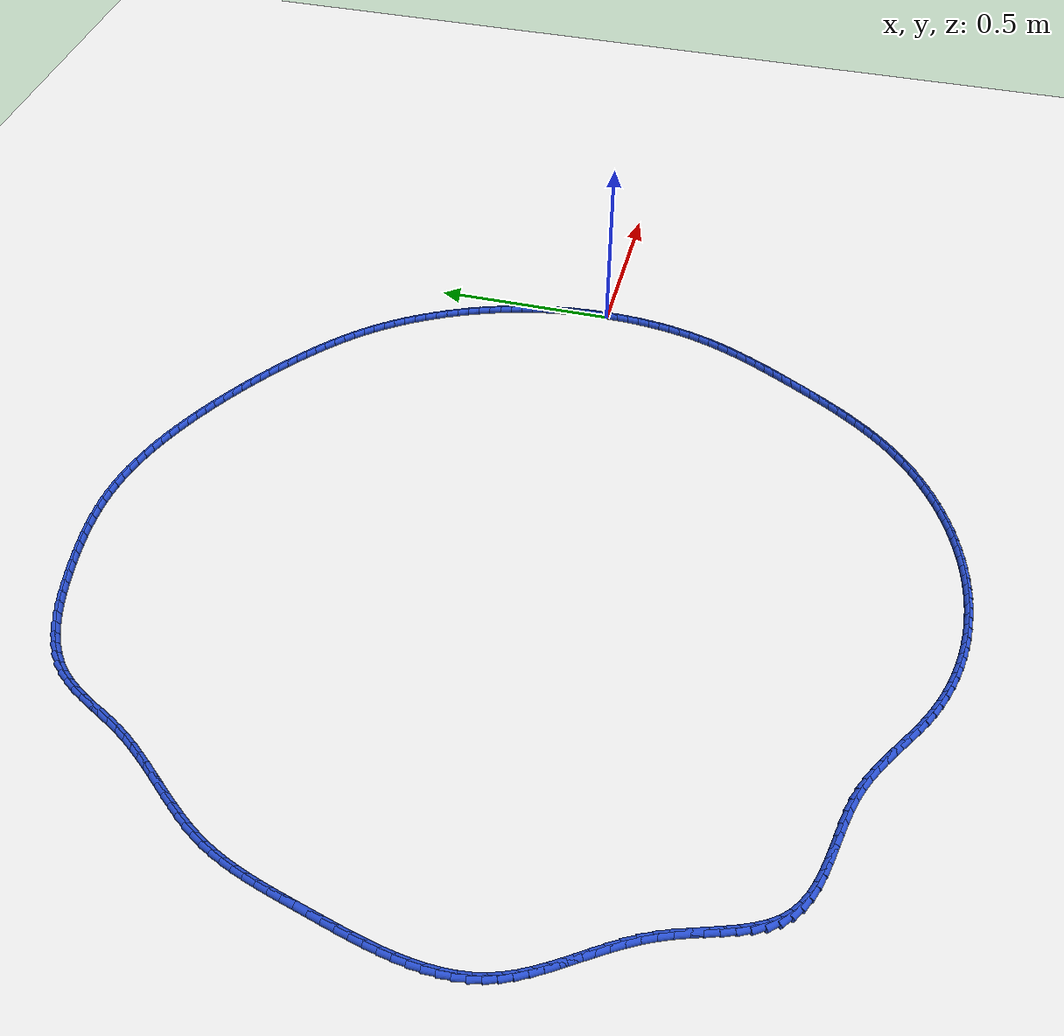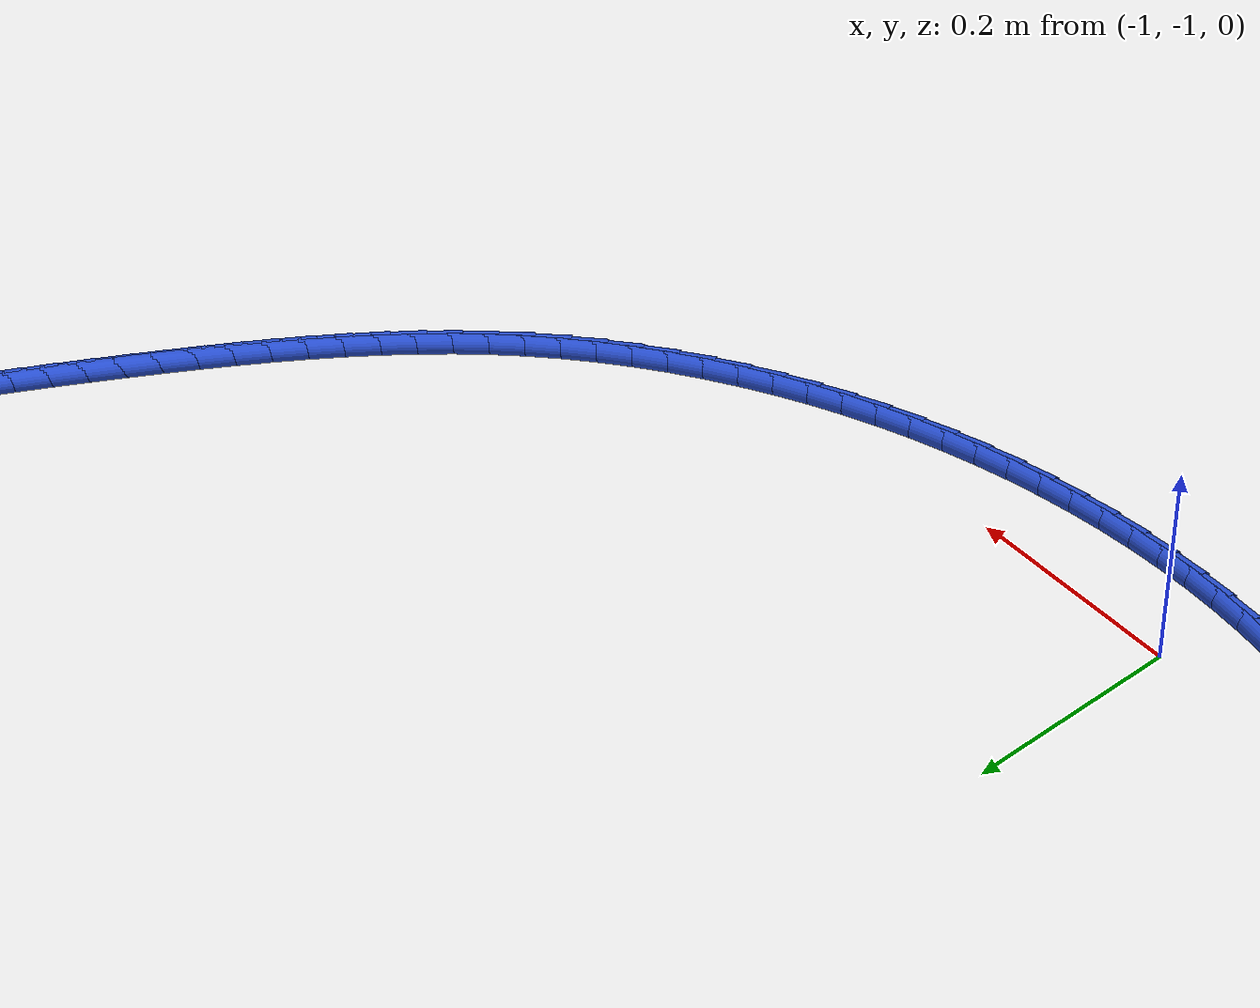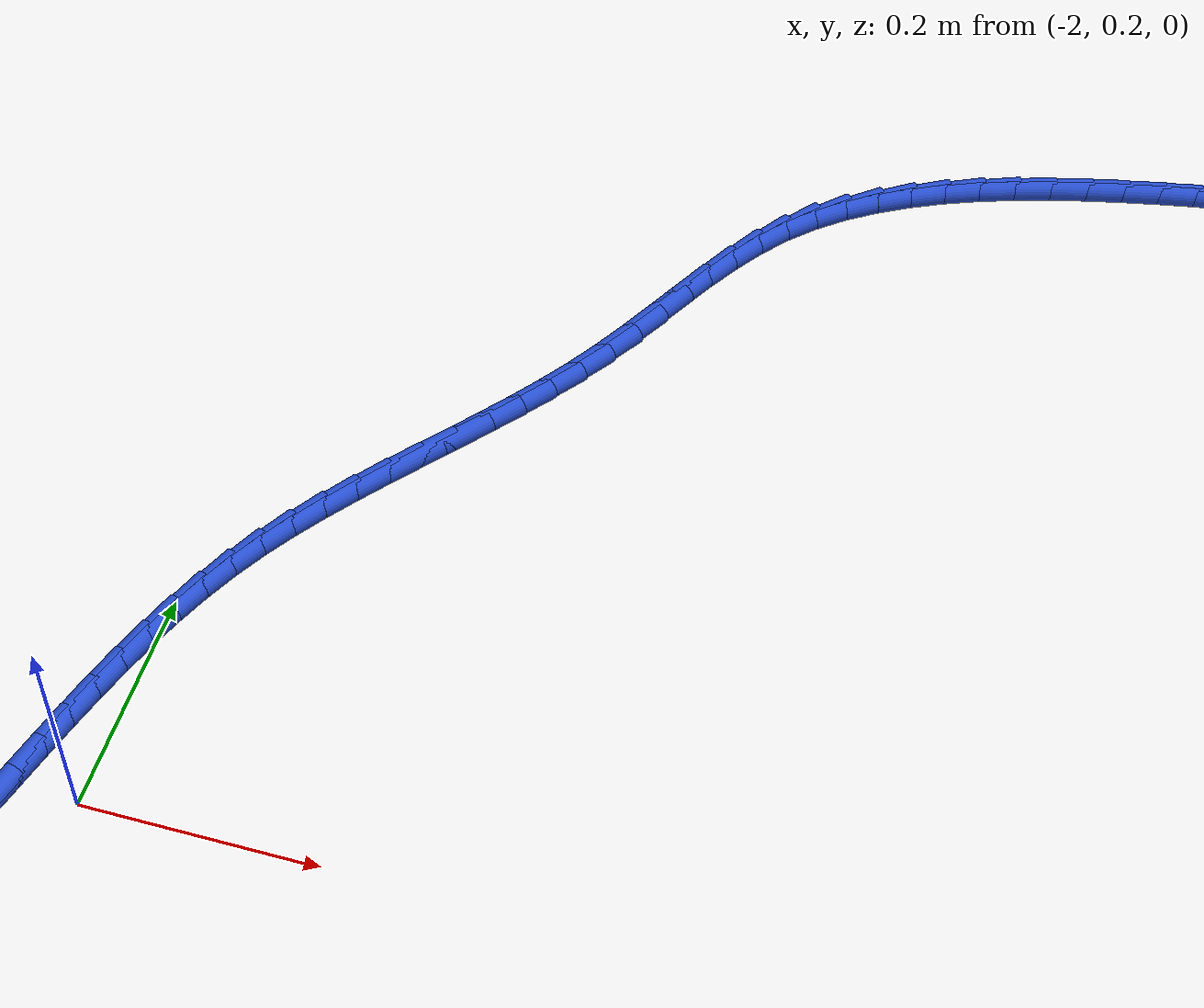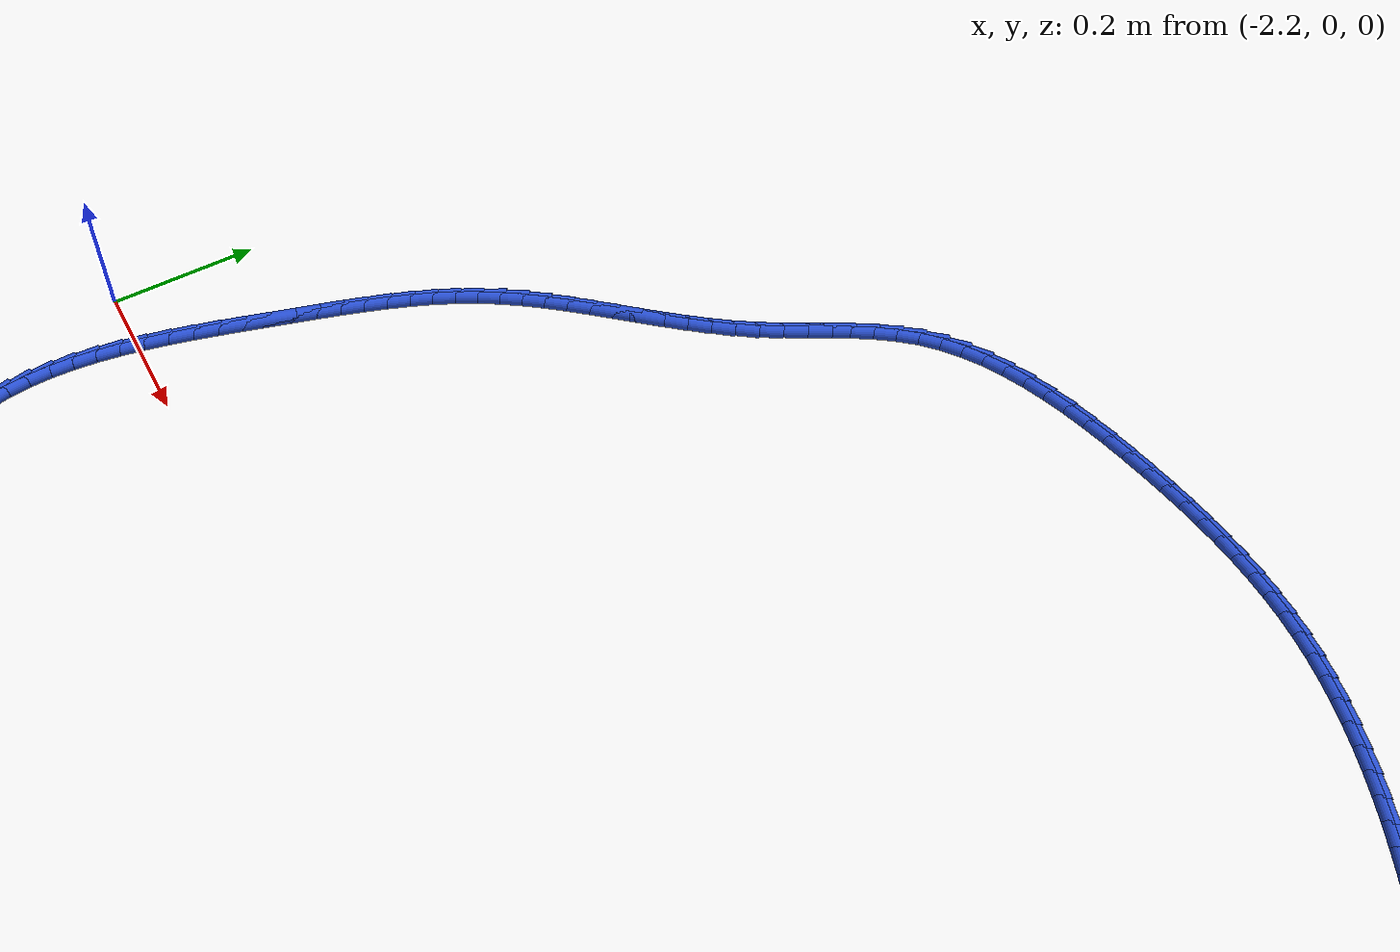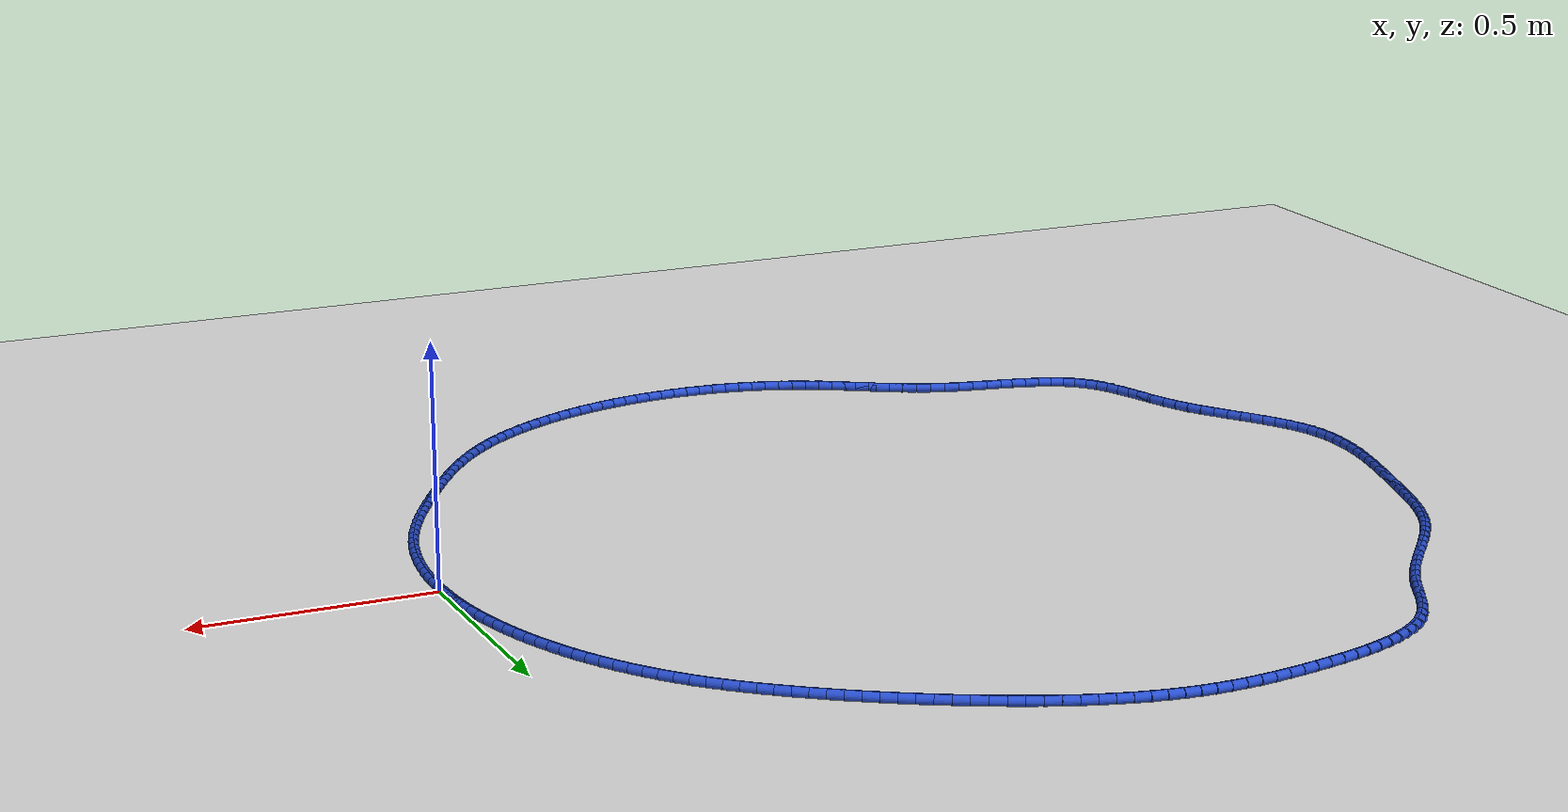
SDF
<sdf version="1.6">
 <world name="default">
  <light name="sun" type="directional">
   <pose>0 0 10 0 -0 0</pose>
   <diffuse>0.8 0.8 0.8 1</diffuse>
   <specular>0.2 0.2 0.2 1</specular>
   <attenuation>
    <range>1000</range>
    <constant>0.9</constant>
    <linear>0.01</linear>
    <quadratic>0.001</quadratic>
   </attenuation>
   <direction>-0.5 0.1 -0.9</direction>
  </light>
  <model name="ground_plane">
   <static>1</static>
   <link name="link">
    <collision name="collision">
     <geometry><plane><normal>0 0 1</normal><size>100 100</size></plane></geometry>
     <surface><friction><ode><mu>100</mu><mu2>50</mu2></ode></friction></surface>
    </collision>
    <visual name="visual">
     <cast_shadows>0</cast_shadows>
     <geometry><plane><normal>0 0 1</normal><size>100 100</size></plane></geometry>
     <material>
      <script><uri>file://media/materials/scripts/gazebo.material</uri><name>Gazebo/WhiteGlow</name></script>
     </material>
    </visual>
   </link>
  </model>
  <gravity>0 0 -9.8</gravity>
  <magnetic_field>6e-06 2.3e-05 -4.2e-05</magnetic_field>
  <atmosphere type="adiabatic"/>
  <physics name="default_physics" default="0" type="ode">
   <max_step_size>0.001</max_step_size>
   <real_time_factor>1</real_time_factor>
   <real_time_update_rate>1000</real_time_update_rate>
  </physics>
  <scene><ambient>0.4 0.4 0.4 1</ambient><background>0.7 0.7 0.7 1</background><shadows>1</shadows></scene>
  <spherical_coordinates>
   <surface_model>EARTH_WGS84</surface_model>
   <latitude_deg>0</latitude_deg>
   <longitude_deg>0</longitude_deg>
   <elevation>0</elevation>
   <heading_deg>0</heading_deg>
  </spherical_coordinates>
  <model name="line">
   <link name="link_0">
    <pose>-7.806255641895632e-18 -6.938893903907228e-17 0.01 0 1.57 -1.5502114497767827</pose>
    <collision name="collision">
     <geometry><cylinder><radius>0.01</radius><length>0.08</length></cylinder></geometry>
    </collision>
    <visual name="visual">
     <material>
      <script><name>Gazebo/Blue</name><uri>file://media/materials/scripts/gazebo.material</uri></script>
     </material>
     <geometry><cylinder><radius>0.01</radius><length>0.08</length></cylinder></geometry>
    </visual>
   </link>
   <link name="link_1">
    <pose>-0.0006545451815906031 0.03179288983349581 0.01 0 1.57 -1.5194112654657008</pose>
    <collision name="collision">
     <geometry><cylinder><radius>0.01</radius><length>0.08</length></cylinder></geometry>
    </collision>
    <visual name="visual">
     <material>
      <script><name>Gazebo/Blue</name><uri>file://media/materials/scripts/gazebo.material</uri></script>
     </material>
     <geometry><cylinder><radius>0.01</radius><length>0.08</length></cylinder></geometry>
    </visual>
   </link>
   <link name="link_2">
    <pose>-0.002285911572315698 0.0635128150894931 0.01 0 1.57 -1.4886612260125327</pose>
    <collision name="collision">
     <geometry><cylinder><radius>0.01</radius><length>0.08</length></cylinder></geometry>
    </collision>
    <visual name="visual">
     <material>
      <script><name>Gazebo/Blue</name><uri>file://media/materials/scripts/gazebo.material</uri></script>
     </material>
     <geometry><cylinder><radius>0.01</radius><length>0.08</length></cylinder></geometry>
    </visual>
   </link>
   <link name="link_3">
    <pose>-0.004889676211518432 0.09514249386253192 0.01 0 1.57 -1.457968654107246</pose>
    <collision name="collision">
     <geometry><cylinder><radius>0.01</radius><length>0.08</length></cylinder></geometry>
    </collision>
    <visual name="visual">
     <material>
      <script><name>Gazebo/Blue</name><uri>file://media/materials/scripts/gazebo.material</uri></script>
     </material>
     <geometry><cylinder><radius>0.01</radius><length>0.08</length></cylinder></geometry>
    </visual>
   </link>
   <link name="link_4">
    <pose>-0.008461416138541959 0.1266646442471523 0.01 0 1.57 -1.4273402913055626</pose>
    <collision name="collision">
     <geometry><cylinder><radius>0.01</radius><length>0.08</length></cylinder></geometry>
    </collision>
    <visual name="visual">
     <material>
      <script><name>Gazebo/Blue</name><uri>file://media/materials/scripts/gazebo.material</uri></script>
     </material>
     <geometry><cylinder><radius>0.01</radius><length>0.08</length></cylinder></geometry>
    </visual>
   </link>
   <link name="link_5">
    <pose>-0.012996708392729426 0.1580619843378943 0.01 0 1.57 -1.3967823265356045</pose>
    <collision name="collision">
     <geometry><cylinder><radius>0.01</radius><length>0.08</length></cylinder></geometry>
    </collision>
    <visual name="visual">
     <material>
      <script><name>Gazebo/Blue</name><uri>file://media/materials/scripts/gazebo.material</uri></script>
     </material>
     <geometry><cylinder><radius>0.01</radius><length>0.08</length></cylinder></geometry>
    </visual>
   </link>
   <link name="link_6">
    <pose>-0.018491130013423993 0.18931723222929817 0.01 0 1.57 -1.366300429166947</pose>
    <collision name="collision">
     <geometry><cylinder><radius>0.01</radius><length>0.08</length></cylinder></geometry>
    </collision>
    <visual name="visual">
     <material>
      <script><name>Gazebo/Blue</name><uri>file://media/materials/scripts/gazebo.material</uri></script>
     </material>
     <geometry><cylinder><radius>0.01</radius><length>0.08</length></cylinder></geometry>
    </visual>
   </link>
   <link name="link_7">
    <pose>-0.024940258039968806 0.22041310601590383 0.01 0 1.57 -1.3358997859574688</pose>
    <collision name="collision">
     <geometry><cylinder><radius>0.01</radius><length>0.08</length></cylinder></geometry>
    </collision>
    <visual name="visual">
     <material>
      <script><name>Gazebo/Blue</name><uri>file://media/materials/scripts/gazebo.material</uri></script>
     </material>
     <geometry><cylinder><radius>0.01</radius><length>0.08</length></cylinder></geometry>
    </visual>
   </link>
   <link name="link_8">
    <pose>-0.03233966951170701 0.2513323237922514 0.01 0 1.57 -1.305585141182004</pose>
    <collision name="collision">
     <geometry><cylinder><radius>0.01</radius><length>0.08</length></cylinder></geometry>
    </collision>
    <visual name="visual">
     <material>
      <script><name>Gazebo/Blue</name><uri>file://media/materials/scripts/gazebo.material</uri></script>
     </material>
     <geometry><cylinder><radius>0.01</radius><length>0.08</length></cylinder></geometry>
    </visual>
   </link>
   <link name="link_9">
    <pose>-0.04068494146798177 0.282057603652881 0.01 0 1.57 -1.2753534848538681</pose>
    <collision name="collision">
     <geometry><cylinder><radius>0.01</radius><length>0.08</length></cylinder></geometry>
    </collision>
    <visual name="visual">
     <material>
      <script><name>Gazebo/Blue</name><uri>file://media/materials/scripts/gazebo.material</uri></script>
     </material>
     <geometry><cylinder><radius>0.01</radius><length>0.08</length></cylinder></geometry>
    </visual>
   </link>
   <link name="link_10">
    <pose>-0.04997161134263959 0.31257072791308366 0.01 0 1.57 -1.24507595859007</pose>
    <collision name="collision">
     <geometry><cylinder><radius>0.01</radius><length>0.08</length></cylinder></geometry>
    </collision>
    <visual name="visual">
     <material>
      <script><name>Gazebo/Blue</name><uri>file://media/materials/scripts/gazebo.material</uri></script>
     </material>
     <geometry><cylinder><radius>0.01</radius><length>0.08</length></cylinder></geometry>
    </visual>
   </link>
   <link name="link_11">
    <pose>-0.06019458662923318 0.3428385949678555 0.01 0 1.57 -1.2145991080721594</pose>
    <collision name="collision">
     <geometry><cylinder><radius>0.01</radius><length>0.08</length></cylinder></geometry>
    </collision>
    <visual name="visual">
     <material>
      <script><name>Gazebo/Blue</name><uri>file://media/materials/scripts/gazebo.material</uri></script>
     </material>
     <geometry><cylinder><radius>0.01</radius><length>0.08</length></cylinder></geometry>
    </visual>
   </link>
   <link name="link_12">
    <pose>-0.07134827006406931 0.37281617705555664 0.01 0 1.57 -1.1838501128964576</pose>
    <collision name="collision">
     <geometry><cylinder><radius>0.01</radius><length>0.08</length></cylinder></geometry>
    </collision>
    <visual name="visual">
     <material>
      <script><name>Gazebo/Blue</name><uri>file://media/materials/scripts/gazebo.material</uri></script>
     </material>
     <geometry><cylinder><radius>0.01</radius><length>0.08</length></cylinder></geometry>
    </visual>
   </link>
   <link name="link_13">
    <pose>-0.08342705020042383 0.40245811130484677 0.01 0 1.57 -1.1527600652654522</pose>
    <collision name="collision">
     <geometry><cylinder><radius>0.01</radius><length>0.08</length></cylinder></geometry>
    </collision>
    <visual name="visual">
     <material>
      <script><name>Gazebo/Blue</name><uri>file://media/materials/scripts/gazebo.material</uri></script>
     </material>
     <geometry><cylinder><radius>0.01</radius><length>0.08</length></cylinder></geometry>
    </visual>
   </link>
   <link name="link_14">
    <pose>-0.0964253155915726 0.4317190348443852 0.01 0 1.57 -1.1212614168789854</pose>
    <collision name="collision">
     <geometry><cylinder><radius>0.01</radius><length>0.08</length></cylinder></geometry>
    </collision>
    <visual name="visual">
     <material>
      <script><name>Gazebo/Blue</name><uri>file://media/materials/scripts/gazebo.material</uri></script>
     </material>
     <geometry><cylinder><radius>0.01</radius><length>0.08</length></cylinder></geometry>
    </visual>
   </link>
   <link name="link_15">
    <pose>-0.11033745479079128 0.4605535848028308 0.01 0 1.57 -1.089288135667351</pose>
    <collision name="collision">
     <geometry><cylinder><radius>0.01</radius><length>0.08</length></cylinder></geometry>
    </collision>
    <visual name="visual">
     <material>
      <script><name>Gazebo/Blue</name><uri>file://media/materials/scripts/gazebo.material</uri></script>
     </material>
     <geometry><cylinder><radius>0.01</radius><length>0.08</length></cylinder></geometry>
    </visual>
   </link>
   <link name="link_16">
    <pose>-0.1251578563513557 0.48891639830884326 0.01 0 1.57 -1.0567759505171306</pose>
    <collision name="collision">
     <geometry><cylinder><radius>0.01</radius><length>0.08</length></cylinder></geometry>
    </collision>
    <visual name="visual">
     <material>
      <script><name>Gazebo/Blue</name><uri>file://media/materials/scripts/gazebo.material</uri></script>
     </material>
     <geometry><cylinder><radius>0.01</radius><length>0.08</length></cylinder></geometry>
    </visual>
   </link>
   <link name="link_17">
    <pose>-0.14088090882654172 0.5167621124910818 0.01 0 1.57 -1.0236626960776993</pose>
    <collision name="collision">
     <geometry><cylinder><radius>0.01</radius><length>0.08</length></cylinder></geometry>
    </collision>
    <visual name="visual">
     <material>
      <script><name>Gazebo/Blue</name><uri>file://media/materials/scripts/gazebo.material</uri></script>
     </material>
     <geometry><cylinder><radius>0.01</radius><length>0.08</length></cylinder></geometry>
    </visual>
   </link>
   <link name="link_18">
    <pose>-0.1575010007696251 0.5440453644782058 0.01 0 1.57 -0.9898887694961618</pose>
    <collision name="collision">
     <geometry><cylinder><radius>0.01</radius><length>0.08</length></cylinder></geometry>
    </collision>
    <visual name="visual">
     <material>
      <script><name>Gazebo/Blue</name><uri>file://media/materials/scripts/gazebo.material</uri></script>
     </material>
     <geometry><cylinder><radius>0.01</radius><length>0.08</length></cylinder></geometry>
    </visual>
   </link>
   <link name="link_19">
    <pose>-0.17501252073388165 0.5707207913988745 0.01 0 1.57 -0.9553977100250496</pose>
    <collision name="collision">
     <geometry><cylinder><radius>0.01</radius><length>0.08</length></cylinder></geometry>
    </collision>
    <visual name="visual">
     <material>
      <script><name>Gazebo/Blue</name><uri>file://media/materials/scripts/gazebo.material</uri></script>
     </material>
     <geometry><cylinder><radius>0.01</radius><length>0.08</length></cylinder></geometry>
    </visual>
   </link>
   <link name="link_20">
    <pose>-0.19340985727258714 0.5967430303817474 0.01 0 1.57 -0.920136910584191</pose>
    <collision name="collision">
     <geometry><cylinder><radius>0.01</radius><length>0.08</length></cylinder></geometry>
    </collision>
    <visual name="visual">
     <material>
      <script><name>Gazebo/Blue</name><uri>file://media/materials/scripts/gazebo.material</uri></script>
     </material>
     <geometry><cylinder><radius>0.01</radius><length>0.08</length></cylinder></geometry>
    </visual>
   </link>
   <link name="link_21">
    <pose>-0.21268739893901734 0.6220667185554833 0.01 0 1.57 -0.8840584672052518</pose>
    <collision name="collision">
     <geometry><cylinder><radius>0.01</radius><length>0.08</length></cylinder></geometry>
    </collision>
    <visual name="visual">
     <material>
      <script><name>Gazebo/Blue</name><uri>file://media/materials/scripts/gazebo.material</uri></script>
     </material>
     <geometry><cylinder><radius>0.01</radius><length>0.08</length></cylinder></geometry>
    </visual>
   </link>
   <link name="link_22">
    <pose>-0.23283953428644816 0.6466464930487423 0.01 0 1.57 -0.8471201674985427</pose>
    <collision name="collision">
     <geometry><cylinder><radius>0.01</radius><length>0.08</length></cylinder></geometry>
    </collision>
    <visual name="visual">
     <material>
      <script><name>Gazebo/Blue</name><uri>file://media/materials/scripts/gazebo.material</uri></script>
     </material>
     <geometry><cylinder><radius>0.01</radius><length>0.08</length></cylinder></geometry>
    </visual>
   </link>
   <link name="link_23">
    <pose>-0.25386065186815526 0.6704369909901832 0.01 0 1.57 -0.8098700248881961</pose>
    <collision name="collision">
     <geometry><cylinder><radius>0.01</radius><length>0.08</length></cylinder></geometry>
    </collision>
    <visual name="visual">
     <material>
      <script><name>Gazebo/Blue</name><uri>file://media/materials/scripts/gazebo.material</uri></script>
     </material>
     <geometry><cylinder><radius>0.01</radius><length>0.08</length></cylinder></geometry>
    </visual>
   </link>
   <link name="link_24">
    <pose>-0.27573358890977906 0.6934075510010748 0.01 0 1.57 -0.7748713112820093</pose>
    <collision name="collision">
     <geometry><cylinder><radius>0.01</radius><length>0.08</length></cylinder></geometry>
    </collision>
    <visual name="visual">
     <material>
      <script><name>Gazebo/Blue</name><uri>file://media/materials/scripts/gazebo.material</uri></script>
     </material>
     <geometry><cylinder><radius>0.01</radius><length>0.08</length></cylinder></geometry>
    </visual>
   </link>
   <link name="link_25">
    <pose>-0.2983903285680832 0.7155922341953169 0.01 0 1.57 -0.7428464093929975</pose>
    <collision name="collision">
     <geometry><cylinder><radius>0.01</radius><length>0.08</length></cylinder></geometry>
    </collision>
    <visual name="visual">
     <material>
      <script><name>Gazebo/Blue</name><uri>file://media/materials/scripts/gazebo.material</uri></script>
     </material>
     <geometry><cylinder><radius>0.01</radius><length>0.08</length></cylinder></geometry>
    </visual>
   </link>
   <link name="link_26">
    <pose>-0.32174886369677025 0.7370429072883423 0.01 0 1.57 -0.7137885605874472</pose>
    <collision name="collision">
     <geometry><cylinder><radius>0.01</radius><length>0.08</length></cylinder></geometry>
    </collision>
    <visual name="visual">
     <material>
      <script><name>Gazebo/Blue</name><uri>file://media/materials/scripts/gazebo.material</uri></script>
     </material>
     <geometry><cylinder><radius>0.01</radius><length>0.08</length></cylinder></geometry>
    </visual>
   </link>
   <link name="link_27">
    <pose>-0.34572718673480757 0.7578114375234223 0.01 0 1.57 -0.6876719097140062</pose>
    <collision name="collision">
     <geometry><cylinder><radius>0.01</radius><length>0.08</length></cylinder></geometry>
    </collision>
    <visual name="visual">
     <material>
      <script><name>Gazebo/Blue</name><uri>file://media/materials/scripts/gazebo.material</uri></script>
     </material>
     <geometry><cylinder><radius>0.01</radius><length>0.08</length></cylinder></geometry>
    </visual>
   </link>
   <link name="link_28">
    <pose>-0.37024329012116175 0.7779496921438275 0.01 0 1.57 -0.6644592457589734</pose>
    <collision name="collision">
     <geometry><cylinder><radius>0.01</radius><length>0.08</length></cylinder></geometry>
    </collision>
    <visual name="visual">
     <material>
      <script><name>Gazebo/Blue</name><uri>file://media/materials/scripts/gazebo.material</uri></script>
     </material>
     <geometry><cylinder><radius>0.01</radius><length>0.08</length></cylinder></geometry>
    </visual>
   </link>
   <link name="link_29">
    <pose>-0.3952151662948001 0.7975095383928291 0.01 0 1.57 -0.6441087234102072</pose>
    <collision name="collision">
     <geometry><cylinder><radius>0.01</radius><length>0.08</length></cylinder></geometry>
    </collision>
    <visual name="visual">
     <material>
      <script><name>Gazebo/Blue</name><uri>file://media/materials/scripts/gazebo.material</uri></script>
     </material>
     <geometry><cylinder><radius>0.01</radius><length>0.08</length></cylinder></geometry>
    </visual>
   </link>
   <link name="link_30">
    <pose>-0.4205608076946896 0.8165428435136987 0.01 0 1.57 -0.6265040001483397</pose>
    <collision name="collision">
     <geometry><cylinder><radius>0.01</radius><length>0.08</length></cylinder></geometry>
    </collision>
    <visual name="visual">
     <material>
      <script><name>Gazebo/Blue</name><uri>file://media/materials/scripts/gazebo.material</uri></script>
     </material>
     <geometry><cylinder><radius>0.01</radius><length>0.08</length></cylinder></geometry>
    </visual>
   </link>
   <link name="link_31">
    <pose>-0.4462006465220543 0.8351002875811697 0.01 0 1.57 -0.6101104772405974</pose>
    <collision name="collision">
     <geometry><cylinder><radius>0.01</radius><length>0.08</length></cylinder></geometry>
    </collision>
    <visual name="visual">
     <material>
      <script><name>Gazebo/Blue</name><uri>file://media/materials/scripts/gazebo.material</uri></script>
     </material>
     <geometry><cylinder><radius>0.01</radius><length>0.08</length></cylinder></geometry>
    </visual>
   </link>
   <link name="link_32">
    <pose>-0.47210389348806636 0.8532088154424396 0.01 0 1.57 -0.5935541881242229</pose>
    <collision name="collision">
     <geometry><cylinder><radius>0.01</radius><length>0.08</length></cylinder></geometry>
    </collision>
    <visual name="visual">
     <material>
      <script><name>Gazebo/Blue</name><uri>file://media/materials/scripts/gazebo.material</uri></script>
     </material>
     <geometry><cylinder><radius>0.01</radius><length>0.08</length></cylinder></geometry>
    </visual>
   </link>
   <link name="link_33">
    <pose>-0.49828478001699494 0.8708734652306569 0.01 0 1.57 -0.5768158917506926</pose>
    <collision name="collision">
     <geometry><cylinder><radius>0.01</radius><length>0.08</length></cylinder></geometry>
    </collision>
    <visual name="visual">
     <material>
      <script><name>Gazebo/Blue</name><uri>file://media/materials/scripts/gazebo.material</uri></script>
     </material>
     <geometry><cylinder><radius>0.01</radius><length>0.08</length></cylinder></geometry>
    </visual>
   </link>
   <link name="link_34">
    <pose>-0.5247592242215289 0.8880984543500565 0.01 0 1.57 -0.5599297688746632</pose>
    <collision name="collision">
     <geometry><cylinder><radius>0.01</radius><length>0.08</length></cylinder></geometry>
    </collision>
    <visual name="visual">
     <material>
      <script><name>Gazebo/Blue</name><uri>file://media/materials/scripts/gazebo.material</uri></script>
     </material>
     <geometry><cylinder><radius>0.01</radius><length>0.08</length></cylinder></geometry>
    </visual>
   </link>
   <link name="link_35">
    <pose>-0.5515431442143576 0.904888000204874 0.01 0 1.57 -0.5429308938090822</pose>
    <collision name="collision">
     <geometry><cylinder><radius>0.01</radius><length>0.08</length></cylinder></geometry>
    </collision>
    <visual name="visual">
     <material>
      <script><name>Gazebo/Blue</name><uri>file://media/materials/scripts/gazebo.material</uri></script>
     </material>
     <geometry><cylinder><radius>0.01</radius><length>0.08</length></cylinder></geometry>
    </visual>
   </link>
   <link name="link_36">
    <pose>-0.5786524581081697 0.9212463201993442 0.01 0 1.57 -0.5258549382365724</pose>
    <collision name="collision">
     <geometry><cylinder><radius>0.01</radius><length>0.08</length></cylinder></geometry>
    </collision>
    <visual name="visual">
     <material>
      <script><name>Gazebo/Blue</name><uri>file://media/materials/scripts/gazebo.material</uri></script>
     </material>
     <geometry><cylinder><radius>0.01</radius><length>0.08</length></cylinder></geometry>
    </visual>
   </link>
   <link name="link_37">
    <pose>-0.606103084015655 0.9371776317377031 0.01 0 1.57 -0.5087378634928827</pose>
    <collision name="collision">
     <geometry><cylinder><radius>0.01</radius><length>0.08</length></cylinder></geometry>
    </collision>
    <visual name="visual">
     <material>
      <script><name>Gazebo/Blue</name><uri>file://media/materials/scripts/gazebo.material</uri></script>
     </material>
     <geometry><cylinder><radius>0.01</radius><length>0.08</length></cylinder></geometry>
    </visual>
   </link>
   <link name="link_38">
    <pose>-0.6339109400495029 0.9526861522241856 0.01 0 1.57 -0.4916105940726589</pose>
    <collision name="collision">
     <geometry><cylinder><radius>0.01</radius><length>0.08</length></cylinder></geometry>
    </collision>
    <visual name="visual">
     <material>
      <script><name>Gazebo/Blue</name><uri>file://media/materials/scripts/gazebo.material</uri></script>
     </material>
     <geometry><cylinder><radius>0.01</radius><length>0.08</length></cylinder></geometry>
    </visual>
   </link>
   <link name="link_39">
    <pose>-0.6620918290638366 0.9677758555477987 0.01 0 1.57 -0.47391634378354275</pose>
    <collision name="collision">
     <geometry><cylinder><radius>0.01</radius><length>0.08</length></cylinder></geometry>
    </collision>
    <visual name="visual">
     <material>
      <script><name>Gazebo/Blue</name><uri>file://media/materials/scripts/gazebo.material</uri></script>
     </material>
     <geometry><cylinder><radius>0.01</radius><length>0.08</length></cylinder></geometry>
    </visual>
   </link>
   <link name="link_40">
    <pose>-0.6906481944856637 0.9824224901555072 0.01 0 1.57 -0.454496837106858</pose>
    <collision name="collision">
     <geometry><cylinder><radius>0.01</radius><length>0.08</length></cylinder></geometry>
    </collision>
    <visual name="visual">
     <material>
      <script><name>Gazebo/Blue</name><uri>file://media/materials/scripts/gazebo.material</uri></script>
     </material>
     <geometry><cylinder><radius>0.01</radius><length>0.08</length></cylinder></geometry>
    </visual>
   </link>
   <link name="link_41">
    <pose>-0.7195568435495912 0.9965476410293027 0.01 0 1.57 -0.43314401409990966</pose>
    <collision name="collision">
     <geometry><cylinder><radius>0.01</radius><length>0.08</length></cylinder></geometry>
    </collision>
    <visual name="visual">
     <material>
      <script><name>Gazebo/Blue</name><uri>file://media/materials/scripts/gazebo.material</uri></script>
     </material>
     <geometry><cylinder><radius>0.01</radius><length>0.08</length></cylinder></geometry>
    </visual>
   </link>
   <link name="link_42">
    <pose>-0.7487916808364614 1.0100667605015594 0.01 0 1.57 -0.4097646911040185</pose>
    <collision name="collision">
     <geometry><cylinder><radius>0.01</radius><length>0.08</length></cylinder></geometry>
    </collision>
    <visual name="visual">
     <material>
      <script><name>Gazebo/Blue</name><uri>file://media/materials/scripts/gazebo.material</uri></script>
     </material>
     <geometry><cylinder><radius>0.01</radius><length>0.08</length></cylinder></geometry>
    </visual>
   </link>
   <link name="link_43">
    <pose>-0.7783266109271172 1.0228953009046506 0.01 0 1.57 -0.384255755379786</pose>
    <collision name="collision">
     <geometry><cylinder><radius>0.01</radius><length>0.08</length></cylinder></geometry>
    </collision>
    <visual name="visual">
     <material>
      <script><name>Gazebo/Blue</name><uri>file://media/materials/scripts/gazebo.material</uri></script>
     </material>
     <geometry><cylinder><radius>0.01</radius><length>0.08</length></cylinder></geometry>
    </visual>
   </link>
   <link name="link_44">
    <pose>-0.8081355384024014 1.034948714570951 0.01 0 1.57 -0.35650610102212865</pose>
    <collision name="collision">
     <geometry><cylinder><radius>0.01</radius><length>0.08</length></cylinder></geometry>
    </collision>
    <visual name="visual">
     <material>
      <script><name>Gazebo/Blue</name><uri>file://media/materials/scripts/gazebo.material</uri></script>
     </material>
     <geometry><cylinder><radius>0.01</radius><length>0.08</length></cylinder></geometry>
    </visual>
   </link>
   <link name="link_45">
    <pose>-0.8381923678431558 1.0461424538328332 0.01 0 1.57 -0.32639921860090804</pose>
    <collision name="collision">
     <geometry><cylinder><radius>0.01</radius><length>0.08</length></cylinder></geometry>
    </collision>
    <visual name="visual">
     <material>
      <script><name>Gazebo/Blue</name><uri>file://media/materials/scripts/gazebo.material</uri></script>
     </material>
     <geometry><cylinder><radius>0.01</radius><length>0.08</length></cylinder></geometry>
    </visual>
   </link>
   <link name="link_46">
    <pose>-0.868471003830224 1.0563919710226721 0.01 0 1.57 -0.29381665675163215</pose>
    <collision name="collision">
     <geometry><cylinder><radius>0.01</radius><length>0.08</length></cylinder></geometry>
    </collision>
    <visual name="visual">
     <material>
      <script><name>Gazebo/Blue</name><uri>file://media/materials/scripts/gazebo.material</uri></script>
     </material>
     <geometry><cylinder><radius>0.01</radius><length>0.08</length></cylinder></geometry>
    </visual>
   </link>
   <link name="link_47">
    <pose>-0.8989453509444473 1.0656127184728403 0.01 0 1.57 -0.25864258550777436</pose>
    <collision name="collision">
     <geometry><cylinder><radius>0.01</radius><length>0.08</length></cylinder></geometry>
    </collision>
    <visual name="visual">
     <material>
      <script><name>Gazebo/Blue</name><uri>file://media/materials/scripts/gazebo.material</uri></script>
     </material>
     <geometry><cylinder><radius>0.01</radius><length>0.08</length></cylinder></geometry>
    </visual>
   </link>
   <link name="link_48">
    <pose>-0.9295893137666692 1.0737201485157126 0.01 0 1.57 -0.22076968146013215</pose>
    <collision name="collision">
     <geometry><cylinder><radius>0.01</radius><length>0.08</length></cylinder></geometry>
    </collision>
    <visual name="visual">
     <material>
      <script><name>Gazebo/Blue</name><uri>file://media/materials/scripts/gazebo.material</uri></script>
     </material>
     <geometry><cylinder><radius>0.01</radius><length>0.08</length></cylinder></geometry>
    </visual>
   </link>
   <link name="link_49">
    <pose>-0.9603767968777323 1.0806297134836629 0.01 0 1.57 -0.1801065078164533</pose>
    <collision name="collision">
     <geometry><cylinder><radius>0.01</radius><length>0.08</length></cylinder></geometry>
    </collision>
    <visual name="visual">
     <material>
      <script><name>Gazebo/Blue</name><uri>file://media/materials/scripts/gazebo.material</uri></script>
     </material>
     <geometry><cylinder><radius>0.01</radius><length>0.08</length></cylinder></geometry>
    </visual>
   </link>
   <link name="link_50">
    <pose>-0.9912817048584782 1.0862568657090639 0.01 0 1.57 -0.13658645833084948</pose>
    <collision name="collision">
     <geometry><cylinder><radius>0.01</radius><length>0.08</length></cylinder></geometry>
    </collision>
    <visual name="visual">
     <material>
      <script><name>Gazebo/Blue</name><uri>file://media/materials/scripts/gazebo.material</uri></script>
     </material>
     <geometry><cylinder><radius>0.01</radius><length>0.08</length></cylinder></geometry>
    </visual>
   </link>
   <link name="link_51">
    <pose>-1.0222779422897503 1.0905170575242904 0.01 0 1.57 -0.09030563473771248</pose>
    <collision name="collision">
     <geometry><cylinder><radius>0.01</radius><length>0.08</length></cylinder></geometry>
    </collision>
    <visual name="visual">
     <material>
      <script><name>Gazebo/Blue</name><uri>file://media/materials/scripts/gazebo.material</uri></script>
     </material>
     <geometry><cylinder><radius>0.01</radius><length>0.08</length></cylinder></geometry>
    </visual>
   </link>
   <link name="link_52">
    <pose>-1.0533404211157429 1.0933298246911303 0.01 0 1.57 -0.04409792855692649</pose>
    <collision name="collision">
     <geometry><cylinder><radius>0.01</radius><length>0.08</length></cylinder></geometry>
    </collision>
    <visual name="visual">
     <material>
      <script><name>Gazebo/Blue</name><uri>file://media/materials/scripts/gazebo.material</uri></script>
     </material>
     <geometry><cylinder><radius>0.01</radius><length>0.08</length></cylinder></geometry>
    </visual>
   </link>
   <link name="link_53">
    <pose>-1.0844659059388662 1.0947032845017493 0.01 0 1.57 -0.0008967322215749287</pose>
    <collision name="collision">
     <geometry><cylinder><radius>0.01</radius><length>0.08</length></cylinder></geometry>
    </collision>
    <visual name="visual">
     <material>
      <script><name>Gazebo/Blue</name><uri>file://media/materials/scripts/gazebo.material</uri></script>
     </material>
     <geometry><cylinder><radius>0.01</radius><length>0.08</length></cylinder></geometry>
    </visual>
   </link>
   <link name="link_54">
    <pose>-1.1156723066244603 1.0947312682942643 0.01 0 1.57 0.038955161904047395</pose>
    <collision name="collision">
     <geometry><cylinder><radius>0.01</radius><length>0.08</length></cylinder></geometry>
    </collision>
    <visual name="visual">
     <material>
      <script><name>Gazebo/Blue</name><uri>file://media/materials/scripts/gazebo.material</uri></script>
     </material>
     <geometry><cylinder><radius>0.01</radius><length>0.08</length></cylinder></geometry>
    </visual>
   </link>
   <link name="link_55">
    <pose>-1.1469783988741316 1.0935111171446366 0.01 0 1.57 0.07530611318332632</pose>
    <collision name="collision">
     <geometry><cylinder><radius>0.01</radius><length>0.08</length></cylinder></geometry>
    </collision>
    <visual name="visual">
     <material>
      <script><name>Gazebo/Blue</name><uri>file://media/materials/scripts/gazebo.material</uri></script>
     </material>
     <geometry><cylinder><radius>0.01</radius><length>0.08</length></cylinder></geometry>
    </visual>
   </link>
   <link name="link_56">
    <pose>-1.1784029583894877 1.0911401721288292 0.01 0 1.57 0.10807541034129929</pose>
    <collision name="collision">
     <geometry><cylinder><radius>0.01</radius><length>0.08</length></cylinder></geometry>
    </collision>
    <visual name="visual">
     <material>
      <script><name>Gazebo/Blue</name><uri>file://media/materials/scripts/gazebo.material</uri></script>
     </material>
     <geometry><cylinder><radius>0.01</radius><length>0.08</length></cylinder></geometry>
    </visual>
   </link>
   <link name="link_57">
    <pose>-1.209964760872134 1.087715774322804 0.01 0 1.57 0.13724059520402282</pose>
    <collision name="collision">
     <geometry><cylinder><radius>0.01</radius><length>0.08</length></cylinder></geometry>
    </collision>
    <visual name="visual">
     <material>
      <script><name>Gazebo/Blue</name><uri>file://media/materials/scripts/gazebo.material</uri></script>
     </material>
     <geometry><cylinder><radius>0.01</radius><length>0.08</length></cylinder></geometry>
    </visual>
   </link>
   <link name="link_58">
    <pose>-1.2416825820236777 1.0833352648025236 0.01 0 1.57 0.16282443819244294</pose>
    <collision name="collision">
     <geometry><cylinder><radius>0.01</radius><length>0.08</length></cylinder></geometry>
    </collision>
    <visual name="visual">
     <material>
      <script><name>Gazebo/Blue</name><uri>file://media/materials/scripts/gazebo.material</uri></script>
     </material>
     <geometry><cylinder><radius>0.01</radius><length>0.08</length></cylinder></geometry>
    </visual>
   </link>
   <link name="link_59">
    <pose>-1.2735751975457257 1.0780959846439502 0.01 0 1.57 0.18488274483353775</pose>
    <collision name="collision">
     <geometry><cylinder><radius>0.01</radius><length>0.08</length></cylinder></geometry>
    </collision>
    <visual name="visual">
     <material>
      <script><name>Gazebo/Blue</name><uri>file://media/materials/scripts/gazebo.material</uri></script>
     </material>
     <geometry><cylinder><radius>0.01</radius><length>0.08</length></cylinder></geometry>
    </visual>
   </link>
   <link name="link_60">
    <pose>-1.3056613831398851 1.0720952749230457 0.01 0 1.57 0.20367643807089145</pose>
    <collision name="collision">
     <geometry><cylinder><radius>0.01</radius><length>0.08</length></cylinder></geometry>
    </collision>
    <visual name="visual">
     <material>
      <script><name>Gazebo/Blue</name><uri>file://media/materials/scripts/gazebo.material</uri></script>
     </material>
     <geometry><cylinder><radius>0.01</radius><length>0.08</length></cylinder></geometry>
    </visual>
   </link>
   <link name="link_61">
    <pose>-1.3379547576884103 1.0654253879334639 0.01 0 1.57 0.2238463543688198</pose>
    <collision name="collision">
     <geometry><cylinder><radius>0.01</radius><length>0.08</length></cylinder></geometry>
    </collision>
    <visual name="visual">
     <material>
      <script><name>Gazebo/Blue</name><uri>file://media/materials/scripts/gazebo.material</uri></script>
     </material>
     <geometry><cylinder><radius>0.01</radius><length>0.08</length></cylinder></geometry>
    </visual>
   </link>
   <link name="link_62">
    <pose>-1.3703409669939894 1.0580522913156651 0.01 0 1.57 0.2503490077230713</pose>
    <collision name="collision">
     <geometry><cylinder><radius>0.01</radius><length>0.08</length></cylinder></geometry>
    </collision>
    <visual name="visual">
     <material>
      <script><name>Gazebo/Blue</name><uri>file://media/materials/scripts/gazebo.material</uri></script>
     </material>
     <geometry><cylinder><radius>0.01</radius><length>0.08</length></cylinder></geometry>
    </visual>
   </link>
   <link name="link_63">
    <pose>-1.402572253347309 1.0498103092714695 0.01 0 1.57 0.28382834283144087</pose>
    <collision name="collision">
     <geometry><cylinder><radius>0.01</radius><length>0.08</length></cylinder></geometry>
    </collision>
    <visual name="visual">
     <material>
      <script><name>Gazebo/Blue</name><uri>file://media/materials/scripts/gazebo.material</uri></script>
     </material>
     <geometry><cylinder><radius>0.01</radius><length>0.08</length></cylinder></geometry>
    </visual>
   </link>
   <link name="link_64">
    <pose>-1.4343946155451595 1.0405276048829992 0.01 0 1.57 0.3248893619595012</pose>
    <collision name="collision">
     <geometry><cylinder><radius>0.01</radius><length>0.08</length></cylinder></geometry>
    </collision>
    <visual name="visual">
     <material>
      <script><name>Gazebo/Blue</name><uri>file://media/materials/scripts/gazebo.material</uri></script>
     </material>
     <geometry><cylinder><radius>0.01</radius><length>0.08</length></cylinder></geometry>
    </visual>
   </link>
   <link name="link_65">
    <pose>-1.465554052384331 1.0300323412323766 0.01 0 1.57 0.37429562208140077</pose>
    <collision name="collision">
     <geometry><cylinder><radius>0.01</radius><length>0.08</length></cylinder></geometry>
    </collision>
    <visual name="visual">
     <material>
      <script><name>Gazebo/Blue</name><uri>file://media/materials/scripts/gazebo.material</uri></script>
     </material>
     <geometry><cylinder><radius>0.01</radius><length>0.08</length></cylinder></geometry>
    </visual>
   </link>
   <link name="link_66">
    <pose>-1.4957965626616143 1.0181526814017228 0.01 0 1.57 0.4329248731205369</pose>
    <collision name="collision">
     <geometry><cylinder><radius>0.01</radius><length>0.08</length></cylinder></geometry>
    </collision>
    <visual name="visual">
     <material>
      <script><name>Gazebo/Blue</name><uri>file://media/materials/scripts/gazebo.material</uri></script>
     </material>
     <geometry><cylinder><radius>0.01</radius><length>0.08</length></cylinder></geometry>
    </visual>
   </link>
   <link name="link_67">
    <pose>-1.5248681451737978 1.0047167884731598 0.01 0 1.57 0.5016845514277875</pose>
    <collision name="collision">
     <geometry><cylinder><radius>0.01</radius><length>0.08</length></cylinder></geometry>
    </collision>
    <visual name="visual">
     <material>
      <script><name>Gazebo/Blue</name><uri>file://media/materials/scripts/gazebo.material</uri></script>
     </material>
     <geometry><cylinder><radius>0.01</radius><length>0.08</length></cylinder></geometry>
    </visual>
   </link>
   <link name="link_68">
    <pose>-1.5525147987176735 0.9895528255288094 0.01 0 1.57 0.581363130732538</pose>
    <collision name="collision">
     <geometry><cylinder><radius>0.01</radius><length>0.08</length></cylinder></geometry>
    </collision>
    <visual name="visual">
     <material>
      <script><name>Gazebo/Blue</name><uri>file://media/materials/scripts/gazebo.material</uri></script>
     </material>
     <geometry><cylinder><radius>0.01</radius><length>0.08</length></cylinder></geometry>
    </visual>
   </link>
   <link name="link_69">
    <pose>-1.5784825220900314 0.9724889556507937 0.01 0 1.57 0.6723969665137532</pose>
    <collision name="collision">
     <geometry><cylinder><radius>0.01</radius><length>0.08</length></cylinder></geometry>
    </collision>
    <visual name="visual">
     <material>
      <script><name>Gazebo/Blue</name><uri>file://media/materials/scripts/gazebo.material</uri></script>
     </material>
     <geometry><cylinder><radius>0.01</radius><length>0.08</length></cylinder></geometry>
    </visual>
   </link>
   <link name="link_70">
    <pose>-1.6025173140876607 0.9533533419212343 0.01 0 1.57 0.7745516236602158</pose>
    <collision name="collision">
     <geometry><cylinder><radius>0.01</radius><length>0.08</length></cylinder></geometry>
    </collision>
    <visual name="visual">
     <material>
      <script><name>Gazebo/Blue</name><uri>file://media/materials/scripts/gazebo.material</uri></script>
     </material>
     <geometry><cylinder><radius>0.01</radius><length>0.08</length></cylinder></geometry>
    </visual>
   </link>
   <link name="link_71">
    <pose>-1.6243652925553298 0.9319742460211722 0.01 0 1.57 0.8793820463048583</pose>
    <collision name="collision">
     <geometry><cylinder><radius>0.01</radius><length>0.08</length></cylinder></geometry>
    </collision>
    <visual name="visual">
     <material>
      <script><name>Gazebo/Blue</name><uri>file://media/materials/scripts/gazebo.material</uri></script>
     </material>
     <geometry><cylinder><radius>0.01</radius><length>0.08</length></cylinder></geometry>
    </visual>
   </link>
   <link name="link_72">
    <pose>-1.6439432428092282 0.9083212812828589 0.01 0 1.57 0.9636982147836098</pose>
    <collision name="collision">
     <geometry><cylinder><radius>0.01</radius><length>0.08</length></cylinder></geometry>
    </collision>
    <visual name="visual">
     <material>
      <script><name>Gazebo/Blue</name><uri>file://media/materials/scripts/gazebo.material</uri></script>
     </material>
     <geometry><cylinder><radius>0.01</radius><length>0.08</length></cylinder></geometry>
    </visual>
   </link>
   <link name="link_73">
    <pose>-1.6616792132999214 0.8827875036995595 0.01 0 1.57 1.0235326451121516</pose>
    <collision name="collision">
     <geometry><cylinder><radius>0.01</radius><length>0.08</length></cylinder></geometry>
    </collision>
    <visual name="visual">
     <material>
      <script><name>Gazebo/Blue</name><uri>file://media/materials/scripts/gazebo.material</uri></script>
     </material>
     <geometry><cylinder><radius>0.01</radius><length>0.08</length></cylinder></geometry>
    </visual>
   </link>
   <link name="link_74">
    <pose>-1.6780965827305714 0.8558449244895914 0.01 0 1.57 1.0600431761222424</pose>
    <collision name="collision">
     <geometry><cylinder><radius>0.01</radius><length>0.08</length></cylinder></geometry>
    </collision>
    <visual name="visual">
     <material>
      <script><name>Gazebo/Blue</name><uri>file://media/materials/scripts/gazebo.material</uri></script>
     </material>
     <geometry><cylinder><radius>0.01</radius><length>0.08</length></cylinder></geometry>
    </visual>
   </link>
   <link name="link_75">
    <pose>-1.693718729804342 0.8279655548712703 0.01 0 1.57 1.0744493308386491</pose>
    <collision name="collision">
     <geometry><cylinder><radius>0.01</radius><length>0.08</length></cylinder></geometry>
    </collision>
    <visual name="visual">
     <material>
      <script><name>Gazebo/Blue</name><uri>file://media/materials/scripts/gazebo.material</uri></script>
     </material>
     <geometry><cylinder><radius>0.01</radius><length>0.08</length></cylinder></geometry>
    </visual>
   </link>
   <link name="link_76">
    <pose>-1.7090690332243956 0.7996214060629124 0.01 0 1.57 1.0675052510958196</pose>
    <collision name="collision">
     <geometry><cylinder><radius>0.01</radius><length>0.08</length></cylinder></geometry>
    </collision>
    <visual name="visual">
     <material>
      <script><name>Gazebo/Blue</name><uri>file://media/materials/scripts/gazebo.material</uri></script>
     </material>
     <geometry><cylinder><radius>0.01</radius><length>0.08</length></cylinder></geometry>
    </visual>
   </link>
   <link name="link_77">
    <pose>-1.7246708716938939 0.7712844892828344 0.01 0 1.57 1.0393420455279236</pose>
    <collision name="collision">
     <geometry><cylinder><radius>0.01</radius><length>0.08</length></cylinder></geometry>
    </collision>
    <visual name="visual">
     <material>
      <script><name>Gazebo/Blue</name><uri>file://media/materials/scripts/gazebo.material</uri></script>
     </material>
     <geometry><cylinder><radius>0.01</radius><length>0.08</length></cylinder></geometry>
    </visual>
   </link>
   <link name="link_78">
    <pose>-1.741047623916 0.7434268157493522 0.01 0 1.57 0.993661672398683</pose>
    <collision name="collision">
     <geometry><cylinder><radius>0.01</radius><length>0.08</length></cylinder></geometry>
    </collision>
    <visual name="visual">
     <material>
      <script><name>Gazebo/Blue</name><uri>file://media/materials/scripts/gazebo.material</uri></script>
     </material>
     <geometry><cylinder><radius>0.01</radius><length>0.08</length></cylinder></geometry>
    </visual>
   </link>
   <link name="link_79">
    <pose>-1.7586200967740708 0.7164371209318464 0.01 0 1.57 0.9506767074275583</pose>
    <collision name="collision">
     <geometry><cylinder><radius>0.01</radius><length>0.08</length></cylinder></geometry>
    </collision>
    <visual name="visual">
     <material>
      <script><name>Gazebo/Blue</name><uri>file://media/materials/scripts/gazebo.material</uri></script>
     </material>
     <geometry><cylinder><radius>0.01</radius><length>0.08</length></cylinder></geometry>
    </visual>
   </link>
   <link name="link_80">
    <pose>-1.7772942405837593 0.690286139855223 0.01 0 1.57 0.9169181919532771</pose>
    <collision name="collision">
     <geometry><cylinder><radius>0.01</radius><length>0.08</length></cylinder></geometry>
    </collision>
    <visual name="visual">
     <material>
      <script><name>Gazebo/Blue</name><uri>file://media/materials/scripts/gazebo.material</uri></script>
     </material>
     <geometry><cylinder><radius>0.01</radius><length>0.08</length></cylinder></geometry>
    </visual>
   </link>
   <link name="link_81">
    <pose>-1.7968148099929657 0.6648137364144525 0.01 0 1.57 0.8924375618304707</pose>
    <collision name="collision">
     <geometry><cylinder><radius>0.01</radius><length>0.08</length></cylinder></geometry>
    </collision>
    <visual name="visual">
     <material>
      <script><name>Gazebo/Blue</name><uri>file://media/materials/scripts/gazebo.material</uri></script>
     </material>
     <geometry><cylinder><radius>0.01</radius><length>0.08</length></cylinder></geometry>
    </visual>
   </link>
   <link name="link_82">
    <pose>-1.816926503953172 0.6398597292858401 0.01 0 1.57 0.8772343567361763</pose>
    <collision name="collision">
     <geometry><cylinder><radius>0.01</radius><length>0.08</length></cylinder></geometry>
    </collision>
    <visual name="visual">
     <material>
      <script><name>Gazebo/Blue</name><uri>file://media/materials/scripts/gazebo.material</uri></script>
     </material>
     <geometry><cylinder><radius>0.01</radius><length>0.08</length></cylinder></geometry>
    </visual>
   </link>
   <link name="link_83">
    <pose>-1.8373740214158611 0.6152639371456924 0.01 0 1.57 0.8713218593977275</pose>
    <collision name="collision">
     <geometry><cylinder><radius>0.01</radius><length>0.08</length></cylinder></geometry>
    </collision>
    <visual name="visual">
     <material>
      <script><name>Gazebo/Blue</name><uri>file://media/materials/scripts/gazebo.material</uri></script>
     </material>
     <geometry><cylinder><radius>0.01</radius><length>0.08</length></cylinder></geometry>
    </visual>
   </link>
   <link name="link_84">
    <pose>-1.8579020613325148 0.5908661786703144 0.01 0 1.57 0.8747671919768399</pose>
    <collision name="collision">
     <geometry><cylinder><radius>0.01</radius><length>0.08</length></cylinder></geometry>
    </collision>
    <visual name="visual">
     <material>
      <script><name>Gazebo/Blue</name><uri>file://media/materials/scripts/gazebo.material</uri></script>
     </material>
     <geometry><cylinder><radius>0.01</radius><length>0.08</length></cylinder></geometry>
    </visual>
   </link>
   <link name="link_85">
    <pose>-1.8782553226546177 0.566506272536012 0.01 0 1.57 0.8877085454889176</pose>
    <collision name="collision">
     <geometry><cylinder><radius>0.01</radius><length>0.08</length></cylinder></geometry>
    </collision>
    <visual name="visual">
     <material>
      <script><name>Gazebo/Blue</name><uri>file://media/materials/scripts/gazebo.material</uri></script>
     </material>
     <geometry><cylinder><radius>0.01</radius><length>0.08</length></cylinder></geometry>
    </visual>
   </link>
   <link name="link_86">
    <pose>-1.89817850433365 0.5420240374190913 0.01 0 1.57 0.9103489086072634</pose>
    <collision name="collision">
     <geometry><cylinder><radius>0.01</radius><length>0.08</length></cylinder></geometry>
    </collision>
    <visual name="visual">
     <material>
      <script><name>Gazebo/Blue</name><uri>file://media/materials/scripts/gazebo.material</uri></script>
     </material>
     <geometry><cylinder><radius>0.01</radius><length>0.08</length></cylinder></geometry>
    </visual>
   </link>
   <link name="link_87">
    <pose>-1.9174163053210969 0.5172592919958577 0.01 0 1.57 0.9429233886717237</pose>
    <collision name="collision">
     <geometry><cylinder><radius>0.01</radius><length>0.08</length></cylinder></geometry>
    </collision>
    <visual name="visual">
     <material>
      <script><name>Gazebo/Blue</name><uri>file://media/materials/scripts/gazebo.material</uri></script>
     </material>
     <geometry><cylinder><radius>0.01</radius><length>0.08</length></cylinder></geometry>
    </visual>
   </link>
   <link name="link_88">
    <pose>-1.9357134245684393 0.49205185494261655 0.01 0 1.57 0.9856352594177191</pose>
    <collision name="collision">
     <geometry><cylinder><radius>0.01</radius><length>0.08</length></cylinder></geometry>
    </collision>
    <visual name="visual">
     <material>
      <script><name>Gazebo/Blue</name><uri>file://media/materials/scripts/gazebo.material</uri></script>
     </material>
     <geometry><cylinder><radius>0.01</radius><length>0.08</length></cylinder></geometry>
    </visual>
   </link>
   <link name="link_89">
    <pose>-1.9528145610271608 0.4662415449356742 0.01 0 1.57 1.0383071461539708</pose>
    <collision name="collision">
     <geometry><cylinder><radius>0.01</radius><length>0.08</length></cylinder></geometry>
    </collision>
    <visual name="visual">
     <material>
      <script><name>Gazebo/Blue</name><uri>file://media/materials/scripts/gazebo.material</uri></script>
     </material>
     <geometry><cylinder><radius>0.01</radius><length>0.08</length></cylinder></geometry>
    </visual>
   </link>
   <link name="link_90">
    <pose>-1.9684713385492372 0.43967156175171307 0.01 0 1.57 1.0934983687333055</pose>
    <collision name="collision">
     <geometry><cylinder><radius>0.01</radius><length>0.08</length></cylinder></geometry>
    </collision>
    <visual name="visual">
     <material>
      <script><name>Gazebo/Blue</name><uri>file://media/materials/scripts/gazebo.material</uri></script>
     </material>
     <geometry><cylinder><radius>0.01</radius><length>0.08</length></cylinder></geometry>
    </visual>
   </link>
   <link name="link_91">
    <pose>-1.9826361275115976 0.41228312017163987 0.01 0 1.57 1.1425686386255236</pose>
    <collision name="collision">
     <geometry><cylinder><radius>0.01</radius><length>0.08</length></cylinder></geometry>
    </collision>
    <visual name="visual">
     <material>
      <script><name>Gazebo/Blue</name><uri>file://media/materials/scripts/gazebo.material</uri></script>
     </material>
     <geometry><cylinder><radius>0.01</radius><length>0.08</length></cylinder></geometry>
    </visual>
   </link>
   <link name="link_92">
    <pose>-1.995488208791405 0.3841282246084329 0.01 0 1.57 1.184762545801811</pose>
    <collision name="collision">
     <geometry><cylinder><radius>0.01</radius><length>0.08</length></cylinder></geometry>
    </collision>
    <visual name="visual">
     <material>
      <script><name>Gazebo/Blue</name><uri>file://media/materials/scripts/gazebo.material</uri></script>
     </material>
     <geometry><cylinder><radius>0.01</radius><length>0.08</length></cylinder></geometry>
    </visual>
   </link>
   <link name="link_93">
    <pose>-2.0072190455945833 0.3552648275282453 0.01 0 1.57 1.2199706552939367</pose>
    <collision name="collision">
     <geometry><cylinder><radius>0.01</radius><length>0.08</length></cylinder></geometry>
    </collision>
    <visual name="visual">
     <material>
      <script><name>Gazebo/Blue</name><uri>file://media/materials/scripts/gazebo.material</uri></script>
     </material>
     <geometry><cylinder><radius>0.01</radius><length>0.08</length></cylinder></geometry>
    </visual>
   </link>
   <link name="link_94">
    <pose>-2.018020101127056 0.3257508813972297 0.01 0 1.57 1.2482321865770525</pose>
    <collision name="collision">
     <geometry><cylinder><radius>0.01</radius><length>0.08</length></cylinder></geometry>
    </collision>
    <visual name="visual">
     <material>
      <script><name>Gazebo/Blue</name><uri>file://media/materials/scripts/gazebo.material</uri></script>
     </material>
     <geometry><cylinder><radius>0.01</radius><length>0.08</length></cylinder></geometry>
    </visual>
   </link>
   <link name="link_95">
    <pose>-2.0280828385947474 0.2956443386815381 0.01 0 1.57 1.2696811562173727</pose>
    <collision name="collision">
     <geometry><cylinder><radius>0.01</radius><length>0.08</length></cylinder></geometry>
    </collision>
    <visual name="visual">
     <material>
      <script><name>Gazebo/Blue</name><uri>file://media/materials/scripts/gazebo.material</uri></script>
     </material>
     <geometry><cylinder><radius>0.01</radius><length>0.08</length></cylinder></geometry>
    </visual>
   </link>
   <link name="link_96">
    <pose>-2.037598721203581 0.26500315184732415 0.01 0 1.57 1.284503144871986</pose>
    <collision name="collision">
     <geometry><cylinder><radius>0.01</radius><length>0.08</length></cylinder></geometry>
    </collision>
    <visual name="visual">
     <material>
      <script><name>Gazebo/Blue</name><uri>file://media/materials/scripts/gazebo.material</uri></script>
     </material>
     <geometry><cylinder><radius>0.01</radius><length>0.08</length></cylinder></geometry>
    </visual>
   </link>
   <link name="link_97">
    <pose>-2.0467592121594804 0.23388527336074005 0.01 0 1.57 1.2929041986908916</pose>
    <collision name="collision">
     <geometry><cylinder><radius>0.01</radius><length>0.08</length></cylinder></geometry>
    </collision>
    <visual name="visual">
     <material>
      <script><name>Gazebo/Blue</name><uri>file://media/materials/scripts/gazebo.material</uri></script>
     </material>
     <geometry><cylinder><radius>0.01</radius><length>0.08</length></cylinder></geometry>
    </visual>
   </link>
   <link name="link_98">
    <pose>-2.0557557746683717 0.2023486556879382 0.01 0 1.57 1.295132572178215</pose>
    <collision name="collision">
     <geometry><cylinder><radius>0.01</radius><length>0.08</length></cylinder></geometry>
    </collision>
    <visual name="visual">
     <material>
      <script><name>Gazebo/Blue</name><uri>file://media/materials/scripts/gazebo.material</uri></script>
     </material>
     <geometry><cylinder><radius>0.01</radius><length>0.08</length></cylinder></geometry>
    </visual>
   </link>
   <link name="link_99">
    <pose>-2.0647784094436585 0.17045137681444933 0.01 0 1.57 1.2954520180588465</pose>
    <collision name="collision">
     <geometry><cylinder><radius>0.01</radius><length>0.08</length></cylinder></geometry>
    </collision>
    <visual name="visual">
     <material>
      <script><name>Gazebo/Blue</name><uri>file://media/materials/scripts/gazebo.material</uri></script>
     </material>
     <geometry><cylinder><radius>0.01</radius><length>0.08</length></cylinder></geometry>
    </visual>
   </link>
   <link name="link_100">
    <pose>-2.073872007855445 0.13826396883017134 0.01 0 1.57 1.301348920833544</pose>
    <collision name="collision">
     <geometry><cylinder><radius>0.01</radius><length>0.08</length></cylinder></geometry>
    </collision>
    <visual name="visual">
     <material>
      <script><name>Gazebo/Blue</name><uri>file://media/materials/scripts/gazebo.material</uri></script>
     </material>
     <geometry><cylinder><radius>0.01</radius><length>0.08</length></cylinder></geometry>
    </visual>
   </link>
   <link name="link_101">
    <pose>-2.0828153255999458 0.10587980509340747 0.01 0 1.57 1.313628478560665</pose>
    <collision name="collision">
     <geometry><cylinder><radius>0.01</radius><length>0.08</length></cylinder></geometry>
    </collision>
    <visual name="visual">
     <material>
      <script><name>Gazebo/Blue</name><uri>file://media/materials/scripts/gazebo.material</uri></script>
     </material>
     <geometry><cylinder><radius>0.01</radius><length>0.08</length></cylinder></geometry>
    </visual>
   </link>
   <link name="link_102">
    <pose>-2.0913586224732614 0.07339470464174094 0.01 0 1.57 1.3324628008331085</pose>
    <collision name="collision">
     <geometry><cylinder><radius>0.01</radius><length>0.08</length></cylinder></geometry>
    </collision>
    <visual name="visual">
     <material>
      <script><name>Gazebo/Blue</name><uri>file://media/materials/scripts/gazebo.material</uri></script>
     </material>
     <geometry><cylinder><radius>0.01</radius><length>0.08</length></cylinder></geometry>
    </visual>
   </link>
   <link name="link_103">
    <pose>-2.0992521582714923 0.04090448651275394 0.01 0 1.57 1.3581902044370504</pose>
    <collision name="collision">
     <geometry><cylinder><radius>0.01</radius><length>0.08</length></cylinder></geometry>
    </collision>
    <visual name="visual">
     <material>
      <script><name>Gazebo/Blue</name><uri>file://media/materials/scripts/gazebo.material</uri></script>
     </material>
     <geometry><cylinder><radius>0.01</radius><length>0.08</length></cylinder></geometry>
    </visual>
   </link>
   <link name="link_104">
    <pose>-2.106246192790738 0.008504969744029056 0.01 0 1.57 1.3913069184945528</pose>
    <collision name="collision">
     <geometry><cylinder><radius>0.01</radius><length>0.08</length></cylinder></geometry>
    </collision>
    <visual name="visual">
     <material>
      <script><name>Gazebo/Blue</name><uri>file://media/materials/scripts/gazebo.material</uri></script>
     </material>
     <geometry><cylinder><radius>0.01</radius><length>0.08</length></cylinder></geometry>
    </visual>
   </link>
   <link name="link_105">
    <pose>-2.1120909858270993 -0.02370802662685119 0.01 0 1.57 1.4324524070538862</pose>
    <collision name="collision">
     <geometry><cylinder><radius>0.01</radius><length>0.08</length></cylinder></geometry>
    </collision>
    <visual name="visual">
     <material>
      <script><name>Gazebo/Blue</name><uri>file://media/materials/scripts/gazebo.material</uri></script>
     </material>
     <geometry><cylinder><radius>0.01</radius><length>0.08</length></cylinder></geometry>
    </visual>
   </link>
   <link name="link_106">
    <pose>-2.1165367971766753 -0.05563868356230499 0.01 0 1.57 1.4823787091427376</pose>
    <collision name="collision">
     <geometry><cylinder><radius>0.01</radius><length>0.08</length></cylinder></geometry>
    </collision>
    <visual name="visual">
     <material>
      <script><name>Gazebo/Blue</name><uri>file://media/materials/scripts/gazebo.material</uri></script>
     </material>
     <geometry><cylinder><radius>0.01</radius><length>0.08</length></cylinder></geometry>
    </visual>
   </link>
   <link name="link_107">
    <pose>-2.1193338866355673 -0.08719118202474826 0.01 0 1.57 1.5418896405621123</pose>
    <collision name="collision">
     <geometry><cylinder><radius>0.01</radius><length>0.08</length></cylinder></geometry>
    </collision>
    <visual name="visual">
     <material>
      <script><name>Gazebo/Blue</name><uri>file://media/materials/scripts/gazebo.material</uri></script>
     </material>
     <geometry><cylinder><radius>0.01</radius><length>0.08</length></cylinder></geometry>
    </visual>
   </link>
   <link name="link_108">
    <pose>-2.1202325139998752 -0.11826970297659928 0.01 0 1.57 -1.5298612527166557</pose>
    <collision name="collision">
     <geometry><cylinder><radius>0.01</radius><length>0.08</length></cylinder></geometry>
    </collision>
    <visual name="visual">
     <material>
      <script><name>Gazebo/Blue</name><uri>file://media/materials/scripts/gazebo.material</uri></script>
     </material>
     <geometry><cylinder><radius>0.01</radius><length>0.08</length></cylinder></geometry>
    </visual>
   </link>
   <link name="link_109">
    <pose>-2.118982939065699 -0.14877842738027544 0.01 0 1.57 -1.4491764332873172</pose>
    <collision name="collision">
     <geometry><cylinder><radius>0.01</radius><length>0.08</length></cylinder></geometry>
    </collision>
    <visual name="visual">
     <material>
      <script><name>Gazebo/Blue</name><uri>file://media/materials/scripts/gazebo.material</uri></script>
     </material>
     <geometry><cylinder><radius>0.01</radius><length>0.08</length></cylinder></geometry>
    </visual>
   </link>
   <link name="link_110">
    <pose>-2.115335421629138 -0.17862153619819415 0.01 0 1.57 -1.3576191493984873</pose>
    <collision name="collision">
     <geometry><cylinder><radius>0.01</radius><length>0.08</length></cylinder></geometry>
    </collision>
    <visual name="visual">
     <material>
      <script><name>Gazebo/Blue</name><uri>file://media/materials/scripts/gazebo.material</uri></script>
     </material>
     <geometry><cylinder><radius>0.01</radius><length>0.08</length></cylinder></geometry>
    </visual>
   </link>
   <link name="link_111">
    <pose>-2.1090402214862936 -0.207703210392773 0.01 0 1.57 -1.2576102328374283</pose>
    <collision name="collision">
     <geometry><cylinder><radius>0.01</radius><length>0.08</length></cylinder></geometry>
    </collision>
    <visual name="visual">
     <material>
      <script><name>Gazebo/Blue</name><uri>file://media/materials/scripts/gazebo.material</uri></script>
     </material>
     <geometry><cylinder><radius>0.01</radius><length>0.08</length></cylinder></geometry>
    </visual>
   </link>
   <link name="link_112">
    <pose>-2.099893673395336 -0.23594688507703088 0.01 0 1.57 -1.1664210164329967</pose>
    <collision name="collision">
     <geometry><cylinder><radius>0.01</radius><length>0.08</length></cylinder></geometry>
    </collision>
    <visual name="visual">
     <material>
      <script><name>Gazebo/Blue</name><uri>file://media/materials/scripts/gazebo.material</uri></script>
     </material>
     <geometry><cylinder><radius>0.01</radius><length>0.08</length></cylinder></geometry>
    </visual>
   </link>
   <link name="link_113">
    <pose>-2.0881211690060195 -0.26345529287472674 0.01 0 1.57 -1.0938044893693735</pose>
    <collision name="collision">
     <geometry><cylinder><radius>0.01</radius><length>0.08</length></cylinder></geometry>
    </collision>
    <visual name="visual">
     <material>
      <script><name>Gazebo/Blue</name><uri>file://media/materials/scripts/gazebo.material</uri></script>
     </material>
     <geometry><cylinder><radius>0.01</radius><length>0.08</length></cylinder></geometry>
    </visual>
   </link>
   <link name="link_114">
    <pose>-2.0741814929510136 -0.29042869841920466 0.01 0 1.57 -1.039759959326756</pose>
    <collision name="collision">
     <geometry><cylinder><radius>0.01</radius><length>0.08</length></cylinder></geometry>
    </collision>
    <visual name="visual">
     <material>
      <script><name>Gazebo/Blue</name><uri>file://media/materials/scripts/gazebo.material</uri></script>
     </material>
     <geometry><cylinder><radius>0.01</radius><length>0.08</length></cylinder></geometry>
    </visual>
   </link>
   <link name="link_115">
    <pose>-2.058535763805351 -0.3170683416691421 0.01 0 1.57 -1.0034632878693568</pose>
    <collision name="collision">
     <geometry><cylinder><radius>0.01</radius><length>0.08</length></cylinder></geometry>
    </collision>
    <visual name="visual">
     <material>
      <script><name>Gazebo/Blue</name><uri>file://media/materials/scripts/gazebo.material</uri></script>
     </material>
     <geometry><cylinder><radius>0.01</radius><length>0.08</length></cylinder></geometry>
    </visual>
   </link>
   <link name="link_116">
    <pose>-2.0416451001440654 -0.34357546258321614 0.01 0 1.57 -0.983908097104183</pose>
    <collision name="collision">
     <geometry><cylinder><radius>0.01</radius><length>0.08</length></cylinder></geometry>
    </collision>
    <visual name="visual">
     <material>
      <script><name>Gazebo/Blue</name><uri>file://media/materials/scripts/gazebo.material</uri></script>
     </material>
     <geometry><cylinder><radius>0.01</radius><length>0.08</length></cylinder></geometry>
    </visual>
   </link>
   <link name="link_117">
    <pose>-2.0239706205421917 -0.37015130112010447 0.01 0 1.57 -0.980219849405874</pose>
    <collision name="collision">
     <geometry><cylinder><radius>0.01</radius><length>0.08</length></cylinder></geometry>
    </collision>
    <visual name="visual">
     <material>
      <script><name>Gazebo/Blue</name><uri>file://media/materials/scripts/gazebo.material</uri></script>
     </material>
     <geometry><cylinder><radius>0.01</radius><length>0.08</length></cylinder></geometry>
    </visual>
   </link>
   <link name="link_118">
    <pose>-2.0059734435747627 -0.3969970972384845 0.01 0 1.57 -0.9917824638495201</pose>
    <collision name="collision">
     <geometry><cylinder><radius>0.01</radius><length>0.08</length></cylinder></geometry>
    </collision>
    <visual name="visual">
     <material>
      <script><name>Gazebo/Blue</name><uri>file://media/materials/scripts/gazebo.material</uri></script>
     </material>
     <geometry><cylinder><radius>0.01</radius><length>0.08</length></cylinder></geometry>
    </visual>
   </link>
   <link name="link_119">
    <pose>-1.9881146878168101 -0.42431409089703387 0.01 0 1.57 -1.0182361333028818</pose>
    <collision name="collision">
     <geometry><cylinder><radius>0.01</radius><length>0.08</length></cylinder></geometry>
    </collision>
    <visual name="visual">
     <material>
      <script><name>Gazebo/Blue</name><uri>file://media/materials/scripts/gazebo.material</uri></script>
     </material>
     <geometry><cylinder><radius>0.01</radius><length>0.08</length></cylinder></geometry>
    </visual>
   </link>
   <link name="link_120">
    <pose>-1.970855471843371 -0.45230352205442914 0.01 0 1.57 -1.0593796424566073</pose>
    <collision name="collision">
     <geometry><cylinder><radius>0.01</radius><length>0.08</length></cylinder></geometry>
    </collision>
    <visual name="visual">
     <material>
      <script><name>Gazebo/Blue</name><uri>file://media/materials/scripts/gazebo.material</uri></script>
     </material>
     <geometry><cylinder><radius>0.01</radius><length>0.08</length></cylinder></geometry>
    </visual>
   </link>
   <link name="link_121">
    <pose>-1.954656914229477 -0.48116663066934817 0.01 0 1.57 -1.1149881610161034</pose>
    <collision name="collision">
     <geometry><cylinder><radius>0.01</radius><length>0.08</length></cylinder></geometry>
    </collision>
    <visual name="visual">
     <material>
      <script><name>Gazebo/Blue</name><uri>file://media/materials/scripts/gazebo.material</uri></script>
     </material>
     <geometry><cylinder><radius>0.01</radius><length>0.08</length></cylinder></geometry>
    </visual>
   </link>
   <link name="link_122">
    <pose>-1.9399801335501619 -0.5111046567004682 0.01 0 1.57 -1.1797843106082713</pose>
    <collision name="collision">
     <geometry><cylinder><radius>0.01</radius><length>0.08</length></cylinder></geometry>
    </collision>
    <visual name="visual">
     <material>
      <script><name>Gazebo/Blue</name><uri>file://media/materials/scripts/gazebo.material</uri></script>
     </material>
     <geometry><cylinder><radius>0.01</radius><length>0.08</length></cylinder></geometry>
    </visual>
   </link>
   <link name="link_123">
    <pose>-1.9271522261662057 -0.5422223467181948 0.01 0 1.57 -1.2276845022121634</pose>
    <collision name="collision">
     <geometry><cylinder><radius>0.01</radius><length>0.08</length></cylinder></geometry>
    </collision>
    <visual name="visual">
     <material>
      <script><name>Gazebo/Blue</name><uri>file://media/materials/scripts/gazebo.material</uri></script>
     </material>
     <geometry><cylinder><radius>0.01</radius><length>0.08</length></cylinder></geometry>
    </visual>
   </link>
   <link name="link_124">
    <pose>-1.915765761977743 -0.5740956025237465 0.01 0 1.57 -1.2510714460914532</pose>
    <collision name="collision">
     <geometry><cylinder><radius>0.01</radius><length>0.08</length></cylinder></geometry>
    </collision>
    <visual name="visual">
     <material>
      <script><name>Gazebo/Blue</name><uri>file://media/materials/scripts/gazebo.material</uri></script>
     </material>
     <geometry><cylinder><radius>0.01</radius><length>0.08</length></cylinder></geometry>
    </visual>
   </link>
   <link name="link_125">
    <pose>-1.905162965873061 -0.6061200823776379 0.01 0 1.57 -1.250375404151595</pose>
    <collision name="collision">
     <geometry><cylinder><radius>0.01</radius><length>0.08</length></cylinder></geometry>
    </collision>
    <visual name="visual">
     <material>
      <script><name>Gazebo/Blue</name><uri>file://media/materials/scripts/gazebo.material</uri></script>
     </material>
     <geometry><cylinder><radius>0.01</radius><length>0.08</length></cylinder></geometry>
    </visual>
   </link>
   <link name="link_126">
    <pose>-1.8946858509842048 -0.6376912920800047 0.01 0 1.57 -1.2245277976718114</pose>
    <collision name="collision">
     <geometry><cylinder><radius>0.01</radius><length>0.08</length></cylinder></geometry>
    </collision>
    <visual name="visual">
     <material>
      <script><name>Gazebo/Blue</name><uri>file://media/materials/scripts/gazebo.material</uri></script>
     </material>
     <geometry><cylinder><radius>0.01</radius><length>0.08</length></cylinder></geometry>
    </visual>
   </link>
   <link name="link_127">
    <pose>-1.8836764304432185 -0.6682047374309842 0.01 0 1.57 -1.1707484887882151</pose>
    <collision name="collision">
     <geometry><cylinder><radius>0.01</radius><length>0.08</length></cylinder></geometry>
    </collision>
    <visual name="visual">
     <material>
      <script><name>Gazebo/Blue</name><uri>file://media/materials/scripts/gazebo.material</uri></script>
     </material>
     <geometry><cylinder><radius>0.01</radius><length>0.08</length></cylinder></geometry>
    </visual>
   </link>
   <link name="link_128">
    <pose>-1.8714767173821458 -0.6970559242307128 0.01 0 1.57 -1.0846648332478863</pose>
    <collision name="collision">
     <geometry><cylinder><radius>0.01</radius><length>0.08</length></cylinder></geometry>
    </collision>
    <visual name="visual">
     <material>
      <script><name>Gazebo/Blue</name><uri>file://media/materials/scripts/gazebo.material</uri></script>
     </material>
     <geometry><cylinder><radius>0.01</radius><length>0.08</length></cylinder></geometry>
    </visual>
   </link>
   <link name="link_129">
    <pose>-1.8574287249330317 -0.7236403582793275 0.01 0 1.57 -0.961344321348398</pose>
    <collision name="collision">
     <geometry><cylinder><radius>0.01</radius><length>0.08</length></cylinder></geometry>
    </collision>
    <visual name="visual">
     <material>
      <script><name>Gazebo/Blue</name><uri>file://media/materials/scripts/gazebo.material</uri></script>
     </material>
     <geometry><cylinder><radius>0.01</radius><length>0.08</length></cylinder></geometry>
    </visual>
   </link>
   <link name="link_130">
    <pose>-1.8408744662279202 -0.7473535453769652 0.01 0 1.57 -0.7991631389105909</pose>
    <collision name="collision">
     <geometry><cylinder><radius>0.01</radius><length>0.08</length></cylinder></geometry>
    </collision>
    <visual name="visual">
     <material>
      <script><name>Gazebo/Blue</name><uri>file://media/materials/scripts/gazebo.material</uri></script>
     </material>
     <geometry><cylinder><radius>0.01</radius><length>0.08</length></cylinder></geometry>
    </visual>
   </link>
   <link name="link_131">
    <pose>-1.821171288162189 -0.7676067569066237 0.01 0 1.57 -0.6281732824559855</pose>
    <collision name="collision">
     <geometry><cylinder><radius>0.01</radius><length>0.08</length></cylinder></geometry>
    </collision>
    <visual name="visual">
     <material>
      <script><name>Gazebo/Blue</name><uri>file://media/materials/scripts/gazebo.material</uri></script>
     </material>
     <geometry><cylinder><radius>0.01</radius><length>0.08</length></cylinder></geometry>
    </visual>
   </link>
   <link name="link_132">
    <pose>-1.7981668331787002 -0.7843153671849803 0.01 0 1.57 -0.4862400981056303</pose>
    <collision name="collision">
     <geometry><cylinder><radius>0.01</radius><length>0.08</length></cylinder></geometry>
    </collision>
    <visual name="visual">
     <material>
      <script><name>Gazebo/Blue</name><uri>file://media/materials/scripts/gazebo.material</uri></script>
     </material>
     <geometry><cylinder><radius>0.01</radius><length>0.08</length></cylinder></geometry>
    </visual>
   </link>
   <link name="link_133">
    <pose>-1.7722904253590281 -0.7979928131096269 0.01 0 1.57 -0.37685425965287883</pose>
    <collision name="collision">
     <geometry><cylinder><radius>0.01</radius><length>0.08</length></cylinder></geometry>
    </collision>
    <visual name="visual">
     <material>
      <script><name>Gazebo/Blue</name><uri>file://media/materials/scripts/gazebo.material</uri></script>
     </material>
     <geometry><cylinder><radius>0.01</radius><length>0.08</length></cylinder></geometry>
    </visual>
   </link>
   <link name="link_134">
    <pose>-1.744005167298876 -0.8091872613409612 0.01 0 1.57 -0.2972223131966332</pose>
    <collision name="collision">
     <geometry><cylinder><radius>0.01</radius><length>0.08</length></cylinder></geometry>
    </collision>
    <visual name="visual">
     <material>
      <script><name>Gazebo/Blue</name><uri>file://media/materials/scripts/gazebo.material</uri></script>
     </material>
     <geometry><cylinder><radius>0.01</radius><length>0.08</length></cylinder></geometry>
    </visual>
   </link>
   <link name="link_135">
    <pose>-1.713774161593947 -0.8184468785393814 0.01 0 1.57 -0.24333208645946955</pose>
    <collision name="collision">
     <geometry><cylinder><radius>0.01</radius><length>0.08</length></cylinder></geometry>
    </collision>
    <visual name="visual">
     <material>
      <script><name>Gazebo/Blue</name><uri>file://media/materials/scripts/gazebo.material</uri></script>
     </material>
     <geometry><cylinder><radius>0.01</radius><length>0.08</length></cylinder></geometry>
    </visual>
   </link>
   <link name="link_136">
    <pose>-1.6820605108399451 -0.8263198313652845 0.01 0 1.57 -0.2116832597439761</pose>
    <collision name="collision">
     <geometry><cylinder><radius>0.01</radius><length>0.08</length></cylinder></geometry>
    </collision>
    <visual name="visual">
     <material>
      <script><name>Gazebo/Blue</name><uri>file://media/materials/scripts/gazebo.material</uri></script>
     </material>
     <geometry><cylinder><radius>0.01</radius><length>0.08</length></cylinder></geometry>
    </visual>
   </link>
   <link name="link_137">
    <pose>-1.6493273176325745 -0.8333542864790692 0.01 0 1.57 -0.19988404451143776</pose>
    <collision name="collision">
     <geometry><cylinder><radius>0.01</radius><length>0.08</length></cylinder></geometry>
    </collision>
    <visual name="visual">
     <material>
      <script><name>Gazebo/Blue</name><uri>file://media/materials/scripts/gazebo.material</uri></script>
     </material>
     <geometry><cylinder><radius>0.01</radius><length>0.08</length></cylinder></geometry>
    </visual>
   </link>
   <link name="link_138">
    <pose>-1.6160376845675373 -0.8400984105411322 0.01 0 1.57 -0.2067493455402264</pose>
    <collision name="collision">
     <geometry><cylinder><radius>0.01</radius><length>0.08</length></cylinder></geometry>
    </collision>
    <visual name="visual">
     <material>
      <script><name>Gazebo/Blue</name><uri>file://media/materials/scripts/gazebo.material</uri></script>
     </material>
     <geometry><cylinder><radius>0.01</radius><length>0.08</length></cylinder></geometry>
    </visual>
   </link>
   <link name="link_139">
    <pose>-1.5826547142405394 -0.8471003702118718 0.01 0 1.57 -0.23224270602856495</pose>
    <collision name="collision">
     <geometry><cylinder><radius>0.01</radius><length>0.08</length></cylinder></geometry>
    </collision>
    <visual name="visual">
     <material>
      <script><name>Gazebo/Blue</name><uri>file://media/materials/scripts/gazebo.material</uri></script>
     </material>
     <geometry><cylinder><radius>0.01</radius><length>0.08</length></cylinder></geometry>
    </visual>
   </link>
   <link name="link_140">
    <pose>-1.5496415092472842 -0.8549083321516858 0.01 0 1.57 -0.2773728512154233</pose>
    <collision name="collision">
     <geometry><cylinder><radius>0.01</radius><length>0.08</length></cylinder></geometry>
    </collision>
    <visual name="visual">
     <material>
      <script><name>Gazebo/Blue</name><uri>file://media/materials/scripts/gazebo.material</uri></script>
     </material>
     <geometry><cylinder><radius>0.01</radius><length>0.08</length></cylinder></geometry>
    </visual>
   </link>
   <link name="link_141">
    <pose>-1.5174611721834745 -0.8640704630209717 0.01 0 1.57 -0.3428709488620042</pose>
    <collision name="collision">
     <geometry><cylinder><radius>0.01</radius><length>0.08</length></cylinder></geometry>
    </collision>
    <visual name="visual">
     <material>
      <script><name>Gazebo/Blue</name><uri>file://media/materials/scripts/gazebo.material</uri></script>
     </material>
     <geometry><cylinder><radius>0.01</radius><length>0.08</length></cylinder></geometry>
    </visual>
   </link>
   <link name="link_142">
    <pose>-1.486552896453165 -0.8751038013594635 0.01 0 1.57 -0.41204835850541754</pose>
    <collision name="collision">
     <geometry><cylinder><radius>0.01</radius><length>0.08</length></cylinder></geometry>
    </collision>
    <visual name="visual">
     <material>
      <script><name>Gazebo/Blue</name><uri>file://media/materials/scripts/gazebo.material</uri></script>
     </material>
     <geometry><cylinder><radius>0.01</radius><length>0.08</length></cylinder></geometry>
    </visual>
   </link>
   <link name="link_143">
    <pose>-1.4569760704053167 -0.8880309056861302 0.01 0 1.57 -0.4693176896918656</pose>
    <collision name="collision">
     <geometry><cylinder><radius>0.01</radius><length>0.08</length></cylinder></geometry>
    </collision>
    <visual name="visual">
     <material>
      <script><name>Gazebo/Blue</name><uri>file://media/materials/scripts/gazebo.material</uri></script>
     </material>
     <geometry><cylinder><radius>0.01</radius><length>0.08</length></cylinder></geometry>
    </visual>
   </link>
   <link name="link_144">
    <pose>-1.428486001776951 -0.902478442508258 0.01 0 1.57 -0.5131234020962</pose>
    <collision name="collision">
     <geometry><cylinder><radius>0.01</radius><length>0.08</length></cylinder></geometry>
    </collision>
    <visual name="visual">
     <material>
      <script><name>Gazebo/Blue</name><uri>file://media/materials/scripts/gazebo.material</uri></script>
     </material>
     <geometry><cylinder><radius>0.01</radius><length>0.08</length></cylinder></geometry>
    </visual>
   </link>
   <link name="link_145">
    <pose>-1.4008294691393863 -0.9180619739468812 0.01 0 1.57 -0.5428425959505145</pose>
    <collision name="collision">
     <geometry><cylinder><radius>0.01</radius><length>0.08</length></cylinder></geometry>
    </collision>
    <visual name="visual">
     <material>
      <script><name>Gazebo/Blue</name><uri>file://media/materials/scripts/gazebo.material</uri></script>
     </material>
     <geometry><cylinder><radius>0.01</radius><length>0.08</length></cylinder></geometry>
    </visual>
   </link>
   <link name="link_146">
    <pose>-1.3737532510639445 -0.9343970621230323 0.01 0 1.57 -0.5581691752128007</pose>
    <collision name="collision">
     <geometry><cylinder><radius>0.01</radius><length>0.08</length></cylinder></geometry>
    </collision>
    <visual name="visual">
     <material>
      <script><name>Gazebo/Blue</name><uri>file://media/materials/scripts/gazebo.material</uri></script>
     </material>
     <geometry><cylinder><radius>0.01</radius><length>0.08</length></cylinder></geometry>
    </visual>
   </link>
   <link name="link_147">
    <pose>-1.3470041261219452 -0.9510992691577463 0.01 0 1.57 -0.5589457734124278</pose>
    <collision name="collision">
     <geometry><cylinder><radius>0.01</radius><length>0.08</length></cylinder></geometry>
    </collision>
    <visual name="visual">
     <material>
      <script><name>Gazebo/Blue</name><uri>file://media/materials/scripts/gazebo.material</uri></script>
     </material>
     <geometry><cylinder><radius>0.01</radius><length>0.08</length></cylinder></geometry>
    </visual>
   </link>
   <link name="link_148">
    <pose>-1.3203288728847093 -0.9677841571720566 0.01 0 1.57 -0.5450712551023162</pose>
    <collision name="collision">
     <geometry><cylinder><radius>0.01</radius><length>0.08</length></cylinder></geometry>
    </collision>
    <visual name="visual">
     <material>
      <script><name>Gazebo/Blue</name><uri>file://media/materials/scripts/gazebo.material</uri></script>
     </material>
     <geometry><cylinder><radius>0.01</radius><length>0.08</length></cylinder></geometry>
    </visual>
   </link>
   <link name="link_149">
    <pose>-1.2934742699235557 -0.9840672882869971 0.01 0 1.57 -0.5164973161276467</pose>
    <collision name="collision">
     <geometry><cylinder><radius>0.01</radius><length>0.08</length></cylinder></geometry>
    </collision>
    <visual name="visual">
     <material>
      <script><name>Gazebo/Blue</name><uri>file://media/materials/scripts/gazebo.material</uri></script>
     </material>
     <geometry><cylinder><radius>0.01</radius><length>0.08</length></cylinder></geometry>
    </visual>
   </link>
   <link name="link_150">
    <pose>-1.2661870958098054 -0.9995642246236016 0.01 0 1.57 -0.47335832735883365</pose>
    <collision name="collision">
     <geometry><cylinder><radius>0.01</radius><length>0.08</length></cylinder></geometry>
    </collision>
    <visual name="visual">
     <material>
      <script><name>Gazebo/Blue</name><uri>file://media/materials/scripts/gazebo.material</uri></script>
     </material>
     <geometry><cylinder><radius>0.01</radius><length>0.08</length></cylinder></geometry>
    </visual>
   </link>
   <link name="link_151">
    <pose>-1.2382150073086093 -1.0138914726075459 0.01 0 1.57 -0.42100858054071527</pose>
    <collision name="collision">
     <geometry><cylinder><radius>0.01</radius><length>0.08</length></cylinder></geometry>
    </collision>
    <visual name="visual">
     <material>
      <script><name>Gazebo/Blue</name><uri>file://media/materials/scripts/gazebo.material</uri></script>
     </material>
     <geometry><cylinder><radius>0.01</radius><length>0.08</length></cylinder></geometry>
    </visual>
   </link>
   <link name="link_152">
    <pose>-1.2094179626296855 -1.0267862942101267 0.01 0 1.57 -0.36941268906473373</pose>
    <collision name="collision">
     <geometry><cylinder><radius>0.01</radius><length>0.08</length></cylinder></geometry>
    </collision>
    <visual name="visual">
     <material>
      <script><name>Gazebo/Blue</name><uri>file://media/materials/scripts/gazebo.material</uri></script>
     </material>
     <geometry><cylinder><radius>0.01</radius><length>0.08</length></cylinder></geometry>
    </visual>
   </link>
   <link name="link_153">
    <pose>-1.1798773526316608 -1.0382240535966256 0.01 0 1.57 -0.31951106363570175</pose>
    <collision name="collision">
     <geometry><cylinder><radius>0.01</radius><length>0.08</length></cylinder></geometry>
    </collision>
    <visual name="visual">
     <material>
      <script><name>Gazebo/Blue</name><uri>file://media/materials/scripts/gazebo.material</uri></script>
     </material>
     <geometry><cylinder><radius>0.01</radius><length>0.08</length></cylinder></geometry>
    </visual>
   </link>
   <link name="link_154">
    <pose>-1.1497004798625667 -1.0482079772648525 0.01 0 1.57 -0.2710652555542463</pose>
    <collision name="collision">
     <geometry><cylinder><radius>0.01</radius><length>0.08</length></cylinder></geometry>
    </collision>
    <visual name="visual">
     <material>
      <script><name>Gazebo/Blue</name><uri>file://media/materials/scripts/gazebo.material</uri></script>
     </material>
     <geometry><cylinder><radius>0.01</radius><length>0.08</length></cylinder></geometry>
    </visual>
   </link>
   <link name="link_155">
    <pose>-1.1189946468704353 -1.0567412917126173 0.01 0 1.57 -0.22382793757732689</pose>
    <collision name="collision">
     <geometry><cylinder><radius>0.01</radius><length>0.08</length></cylinder></geometry>
    </collision>
    <visual name="visual">
     <material>
      <script><name>Gazebo/Blue</name><uri>file://media/materials/scripts/gazebo.material</uri></script>
     </material>
     <geometry><cylinder><radius>0.01</radius><length>0.08</length></cylinder></geometry>
    </visual>
   </link>
   <link name="link_156">
    <pose>-1.0878671562032987 -1.063827223437731 0.01 0 1.57 -0.17754585929597175</pose>
    <collision name="collision">
     <geometry><cylinder><radius>0.01</radius><length>0.08</length></cylinder></geometry>
    </collision>
    <visual name="visual">
     <material>
      <script><name>Gazebo/Blue</name><uri>file://media/materials/scripts/gazebo.material</uri></script>
     </material>
     <geometry><cylinder><radius>0.01</radius><length>0.08</length></cylinder></geometry>
    </visual>
   </link>
   <link name="link_157">
    <pose>-1.0564253104091894 -1.0694689989380046 0.01 0 1.57 -0.13203184313995336</pose>
    <collision name="collision">
     <geometry><cylinder><radius>0.01</radius><length>0.08</length></cylinder></geometry>
    </collision>
    <visual name="visual">
     <material>
      <script><name>Gazebo/Blue</name><uri>file://media/materials/scripts/gazebo.material</uri></script>
     </material>
     <geometry><cylinder><radius>0.01</radius><length>0.08</length></cylinder></geometry>
    </visual>
   </link>
   <link name="link_158">
    <pose>-1.0247671750393579 -1.0736733399360774 0.01 0 1.57 -0.0874009356507075</pose>
    <collision name="collision">
     <geometry><cylinder><radius>0.01</radius><length>0.08</length></cylinder></geometry>
    </collision>
    <visual name="visual">
     <material>
      <script><name>Gazebo/Blue</name><uri>file://media/materials/scripts/gazebo.material</uri></script>
     </material>
     <geometry><cylinder><radius>0.01</radius><length>0.08</length></cylinder></geometry>
    </visual>
   </link>
   <link name="link_159">
    <pose>-0.9929538488947914 -1.0764609561537701 0.01 0 1.57 -0.04368289948846643</pose>
    <collision name="collision">
     <geometry><cylinder><radius>0.01</radius><length>0.08</length></cylinder></geometry>
    </collision>
    <visual name="visual">
     <material>
      <script><name>Gazebo/Blue</name><uri>file://media/materials/scripts/gazebo.material</uri></script>
     </material>
     <geometry><cylinder><radius>0.01</radius><length>0.08</length></cylinder></geometry>
    </visual>
   </link>
   <link name="link_160">
    <pose>-0.9610371843957445 -1.0778560560885644 0.01 0 1.57 -0.0008380886207388909</pose>
    <collision name="collision">
     <geometry><cylinder><radius>0.01</radius><length>0.08</length></cylinder></geometry>
    </collision>
    <visual name="visual">
     <material>
      <script><name>Gazebo/Blue</name><uri>file://media/materials/scripts/gazebo.material</uri></script>
     </material>
     <geometry><cylinder><radius>0.01</radius><length>0.08</length></cylinder></geometry>
    </visual>
   </link>
   <link name="link_161">
    <pose>-0.9290690339624715 -1.0778828482379414 0.01 0 1.57 0.04118403340535659</pose>
    <collision name="collision">
     <geometry><cylinder><radius>0.01</radius><length>0.08</length></cylinder></geometry>
    </collision>
    <visual name="visual">
     <material>
      <script><name>Gazebo/Blue</name><uri>file://media/materials/scripts/gazebo.material</uri></script>
     </material>
     <geometry><cylinder><radius>0.01</radius><length>0.08</length></cylinder></geometry>
    </visual>
   </link>
   <link name="link_162">
    <pose>-0.8971012500152273 -1.076565541099383 0.01 0 1.57 0.0824431688421627</pose>
    <collision name="collision">
     <geometry><cylinder><radius>0.01</radius><length>0.08</length></cylinder></geometry>
    </collision>
    <visual name="visual">
     <material>
      <script><name>Gazebo/Blue</name><uri>file://media/materials/scripts/gazebo.material</uri></script>
     </material>
     <geometry><cylinder><radius>0.01</radius><length>0.08</length></cylinder></geometry>
    </visual>
   </link>
   <link name="link_163">
    <pose>-0.8651856849742662 -1.0739283431703712 0.01 0 1.57 0.12300662671594531</pose>
    <collision name="collision">
     <geometry><cylinder><radius>0.01</radius><length>0.08</length></cylinder></geometry>
    </collision>
    <visual name="visual">
     <material>
      <script><name>Gazebo/Blue</name><uri>file://media/materials/scripts/gazebo.material</uri></script>
     </material>
     <geometry><cylinder><radius>0.01</radius><length>0.08</length></cylinder></geometry>
    </visual>
   </link>
   <link name="link_164">
    <pose>-0.8333741912598422 -1.0699954629483863 0.01 0 1.57 0.16294794937993848</pose>
    <collision name="collision">
     <geometry><cylinder><radius>0.01</radius><length>0.08</length></cylinder></geometry>
    </collision>
    <visual name="visual">
     <material>
      <script><name>Gazebo/Blue</name><uri>file://media/materials/scripts/gazebo.material</uri></script>
     </material>
     <geometry><cylinder><radius>0.01</radius><length>0.08</length></cylinder></geometry>
    </visual>
   </link>
   <link name="link_165">
    <pose>-0.8017186212922113 -1.0647911089309108 0.01 0 1.57 0.20234572935290873</pose>
    <collision name="collision">
     <geometry><cylinder><radius>0.01</radius><length>0.08</length></cylinder></geometry>
    </collision>
    <visual name="visual">
     <material>
      <script><name>Gazebo/Blue</name><uri>file://media/materials/scripts/gazebo.material</uri></script>
     </material>
     <geometry><cylinder><radius>0.01</radius><length>0.08</length></cylinder></geometry>
    </visual>
   </link>
   <link name="link_166">
    <pose>-0.7702708274916276 -1.0583394896154263 0.01 0 1.57 0.241282609641058</pose>
    <collision name="collision">
     <geometry><cylinder><radius>0.01</radius><length>0.08</length></cylinder></geometry>
    </collision>
    <visual name="visual">
     <material>
      <script><name>Gazebo/Blue</name><uri>file://media/materials/scripts/gazebo.material</uri></script>
     </material>
     <geometry><cylinder><radius>0.01</radius><length>0.08</length></cylinder></geometry>
    </visual>
   </link>
   <link name="link_167">
    <pose>-0.7390826622783454 -1.050664813499414 0.01 0 1.57 0.2798444525112158</pose>
    <collision name="collision">
     <geometry><cylinder><radius>0.01</radius><length>0.08</length></cylinder></geometry>
    </collision>
    <visual name="visual">
     <material>
      <script><name>Gazebo/Blue</name><uri>file://media/materials/scripts/gazebo.material</uri></script>
     </material>
     <geometry><cylinder><radius>0.01</radius><length>0.08</length></cylinder></geometry>
    </visual>
   </link>
   <link name="link_168">
    <pose>-0.7082059780726193 -1.0417912890803556 0.01 0 1.57 0.318119656093629</pose>
    <collision name="collision">
     <geometry><cylinder><radius>0.01</radius><length>0.08</length></cylinder></geometry>
    </collision>
    <visual name="visual">
     <material>
      <script><name>Gazebo/Blue</name><uri>file://media/materials/scripts/gazebo.material</uri></script>
     </material>
     <geometry><cylinder><radius>0.01</radius><length>0.08</length></cylinder></geometry>
    </visual>
   </link>
   <link name="link_169">
    <pose>-0.677692627294704 -1.0317431248557327 0.01 0 1.57 0.35619859458423875</pose>
    <collision name="collision">
     <geometry><cylinder><radius>0.01</radius><length>0.08</length></cylinder></geometry>
    </collision>
    <visual name="visual">
     <material>
      <script><name>Gazebo/Blue</name><uri>file://media/materials/scripts/gazebo.material</uri></script>
     </material>
     <geometry><cylinder><radius>0.01</radius><length>0.08</length></cylinder></geometry>
    </visual>
   </link>
   <link name="link_170">
    <pose>-0.6475944623648533 -1.020544529323026 0.01 0 1.57 0.3941827308634817</pose>
    <collision name="collision">
     <geometry><cylinder><radius>0.01</radius><length>0.08</length></cylinder></geometry>
    </collision>
    <visual name="visual">
     <material>
      <script><name>Gazebo/Blue</name><uri>file://media/materials/scripts/gazebo.material</uri></script>
     </material>
     <geometry><cylinder><radius>0.01</radius><length>0.08</length></cylinder></geometry>
    </visual>
   </link>
   <link name="link_171">
    <pose>-0.6179633773687094 -1.0082193954959884 0.01 0 1.57 0.43225436680415347</pose>
    <collision name="collision">
     <geometry><cylinder><radius>0.01</radius><length>0.08</length></cylinder></geometry>
    </collision>
    <visual name="visual">
     <material>
      <script><name>Gazebo/Blue</name><uri>file://media/materials/scripts/gazebo.material</uri></script>
     </material>
     <geometry><cylinder><radius>0.01</radius><length>0.08</length></cylinder></geometry>
    </visual>
   </link>
   <link name="link_172">
    <pose>-0.5888516601065892 -0.9947886352429288 0.01 0 1.57 0.4705526410146941</pose>
    <collision name="collision">
     <geometry><cylinder><radius>0.01</radius><length>0.08</length></cylinder></geometry>
    </collision>
    <visual name="visual">
     <material>
      <script><name>Gazebo/Blue</name><uri>file://media/materials/scripts/gazebo.material</uri></script>
     </material>
     <geometry><cylinder><radius>0.01</radius><length>0.08</length></cylinder></geometry>
    </visual>
   </link>
   <link name="link_173">
    <pose>-0.560311815070275 -0.980271519678574 0.01 0 1.57 0.509166251014288</pose>
    <collision name="collision">
     <geometry><cylinder><radius>0.01</radius><length>0.08</length></cylinder></geometry>
    </collision>
    <visual name="visual">
     <material>
      <script><name>Gazebo/Blue</name><uri>file://media/materials/scripts/gazebo.material</uri></script>
     </material>
     <geometry><cylinder><radius>0.01</radius><length>0.08</length></cylinder></geometry>
    </visual>
   </link>
   <link name="link_174">
    <pose>-0.5323963490041438 -0.9646873028613522 0.01 0 1.57 0.548182179735774</pose>
    <collision name="collision">
     <geometry><cylinder><radius>0.01</radius><length>0.08</length></cylinder></geometry>
    </collision>
    <visual name="visual">
     <material>
      <script><name>Gazebo/Blue</name><uri>file://media/materials/scripts/gazebo.material</uri></script>
     </material>
     <geometry><cylinder><radius>0.01</radius><length>0.08</length></cylinder></geometry>
    </visual>
   </link>
   <link name="link_175">
    <pose>-0.5051577686525726 -0.9480552388496922 0.01 0 1.57 0.5876856275205995</pose>
    <collision name="collision">
     <geometry><cylinder><radius>0.01</radius><length>0.08</length></cylinder></geometry>
    </collision>
    <visual name="visual">
     <material>
      <script><name>Gazebo/Blue</name><uri>file://media/materials/scripts/gazebo.material</uri></script>
     </material>
     <geometry><cylinder><radius>0.01</radius><length>0.08</length></cylinder></geometry>
    </visual>
   </link>
   <link name="link_176">
    <pose>-0.478648580759938 -0.9303945817020228 0.01 0 1.57 0.627759301668129</pose>
    <collision name="collision">
     <geometry><cylinder><radius>0.01</radius><length>0.08</length></cylinder></geometry>
    </collision>
    <visual name="visual">
     <material>
      <script><name>Gazebo/Blue</name><uri>file://media/materials/scripts/gazebo.material</uri></script>
     </material>
     <geometry><cylinder><radius>0.01</radius><length>0.08</length></cylinder></geometry>
    </visual>
   </link>
   <link name="link_177">
    <pose>-0.4529212920706184 -0.9117245854767736 0.01 0 1.57 0.6684825547672382</pose>
    <collision name="collision">
     <geometry><cylinder><radius>0.01</radius><length>0.08</length></cylinder></geometry>
    </collision>
    <visual name="visual">
     <material>
      <script><name>Gazebo/Blue</name><uri>file://media/materials/scripts/gazebo.material</uri></script>
     </material>
     <geometry><cylinder><radius>0.01</radius><length>0.08</length></cylinder></geometry>
    </visual>
   </link>
   <link name="link_178">
    <pose>-0.42802840932899017 -0.8920645042323727 0.01 0 1.57 0.7099303481009311</pose>
    <collision name="collision">
     <geometry><cylinder><radius>0.01</radius><length>0.08</length></cylinder></geometry>
    </collision>
    <visual name="visual">
     <material>
      <script><name>Gazebo/Blue</name><uri>file://media/materials/scripts/gazebo.material</uri></script>
     </material>
     <geometry><cylinder><radius>0.01</radius><length>0.08</length></cylinder></geometry>
    </visual>
   </link>
   <link name="link_179">
    <pose>-0.40402243927943077 -0.8714335920272496 0.01 0 1.57 0.7521720212057421</pose>
    <collision name="collision">
     <geometry><cylinder><radius>0.01</radius><length>0.08</length></cylinder></geometry>
    </collision>
    <visual name="visual">
     <material>
      <script><name>Gazebo/Blue</name><uri>file://media/materials/scripts/gazebo.material</uri></script>
     </material>
     <geometry><cylinder><radius>0.01</radius><length>0.08</length></cylinder></geometry>
    </visual>
   </link>
   <link name="link_180">
    <pose>-0.3809558886663171 -0.8498511029198327 0.01 0 1.57 0.7946747848993536</pose>
    <collision name="collision">
     <geometry><cylinder><radius>0.01</radius><length>0.08</length></cylinder></geometry>
    </collision>
    <visual name="visual">
     <material>
      <script><name>Gazebo/Blue</name><uri>file://media/materials/scripts/gazebo.material</uri></script>
     </material>
     <geometry><cylinder><radius>0.01</radius><length>0.08</length></cylinder></geometry>
    </visual>
   </link>
   <link name="link_181">
    <pose>-0.35886318998459654 -0.8273446630420529 0.01 0 1.57 0.8346495669875054</pose>
    <collision name="collision">
     <geometry><cylinder><radius>0.01</radius><length>0.08</length></cylinder></geometry>
    </collision>
    <visual name="visual">
     <material>
      <script><name>Gazebo/Blue</name><uri>file://media/materials/scripts/gazebo.material</uri></script>
     </material>
     <geometry><cylinder><radius>0.01</radius><length>0.08</length></cylinder></geometry>
    </visual>
   </link>
   <link name="link_182">
    <pose>-0.3376945144839702 -0.8039809287130323 0.01 0 1.57 0.8711928192754448</pose>
    <collision name="collision">
     <geometry><cylinder><radius>0.01</radius><length>0.08</length></cylinder></geometry>
    </collision>
    <visual name="visual">
     <material>
      <script><name>Gazebo/Blue</name><uri>file://media/materials/scripts/gazebo.material</uri></script>
     </material>
     <geometry><cylinder><radius>0.01</radius><length>0.08</length></cylinder></geometry>
    </visual>
   </link>
   <link name="link_183">
    <pose>-0.31737549802780024 -0.7798379211530251 0.01 0 1.57 0.9042490874749607</pose>
    <collision name="collision">
     <geometry><cylinder><radius>0.01</radius><length>0.08</length></cylinder></geometry>
    </collision>
    <visual name="visual">
     <material>
      <script><name>Gazebo/Blue</name><uri>file://media/materials/scripts/gazebo.material</uri></script>
     </material>
     <geometry><cylinder><radius>0.01</radius><length>0.08</length></cylinder></geometry>
    </visual>
   </link>
   <link name="link_184">
    <pose>-0.2978317736794297 -0.75499366287927 0.01 0 1.57 0.9338056909596247</pose>
    <collision name="collision">
     <geometry><cylinder><radius>0.01</radius><length>0.08</length></cylinder></geometry>
    </collision>
    <visual name="visual">
     <material>
      <script><name>Gazebo/Blue</name><uri>file://media/materials/scripts/gazebo.material</uri></script>
     </material>
     <geometry><cylinder><radius>0.01</radius><length>0.08</length></cylinder></geometry>
    </visual>
   </link>
   <link name="link_185">
    <pose>-0.2789889745021998 -0.7295261764090036 0.01 0 1.57 0.9598805877064678</pose>
    <collision name="collision">
     <geometry><cylinder><radius>0.01</radius><length>0.08</length></cylinder></geometry>
    </collision>
    <visual name="visual">
     <material>
      <script><name>Gazebo/Blue</name><uri>file://media/materials/scripts/gazebo.material</uri></script>
     </material>
     <geometry><cylinder><radius>0.01</radius><length>0.08</length></cylinder></geometry>
    </visual>
   </link>
   <link name="link_186">
    <pose>-0.2607727335594523 -0.7035134842594629 0.01 0 1.57 0.9825114286327941</pose>
    <collision name="collision">
     <geometry><cylinder><radius>0.01</radius><length>0.08</length></cylinder></geometry>
    </collision>
    <visual name="visual">
     <material>
      <script><name>Gazebo/Blue</name><uri>file://media/materials/scripts/gazebo.material</uri></script>
     </material>
     <geometry><cylinder><radius>0.01</radius><length>0.08</length></cylinder></geometry>
    </visual>
   </link>
   <link name="link_187">
    <pose>-0.24310868391452933 -0.6770336089478854 0.01 0 1.57 1.0017460930779933</pose>
    <collision name="collision">
     <geometry><cylinder><radius>0.01</radius><length>0.08</length></cylinder></geometry>
    </collision>
    <visual name="visual">
     <material>
      <script><name>Gazebo/Blue</name><uri>file://media/materials/scripts/gazebo.material</uri></script>
     </material>
     <geometry><cylinder><radius>0.01</radius><length>0.08</length></cylinder></geometry>
    </visual>
   </link>
   <link name="link_188">
    <pose>-0.2259224586307727 -0.6501645729915085 0.01 0 1.57 1.017634817799439</pose>
    <collision name="collision">
     <geometry><cylinder><radius>0.01</radius><length>0.08</length></cylinder></geometry>
    </collision>
    <visual name="visual">
     <material>
      <script><name>Gazebo/Blue</name><uri>file://media/materials/scripts/gazebo.material</uri></script>
     </material>
     <geometry><cylinder><radius>0.01</radius><length>0.08</length></cylinder></geometry>
    </visual>
   </link>
   <link name="link_189">
    <pose>-0.20913969077152392 -0.6229843989075687 0.01 0 1.57 1.0302238567266893</pose>
    <collision name="collision">
     <geometry><cylinder><radius>0.01</radius><length>0.08</length></cylinder></geometry>
    </collision>
    <visual name="visual">
     <material>
      <script><name>Gazebo/Blue</name><uri>file://media/materials/scripts/gazebo.material</uri></script>
     </material>
     <geometry><cylinder><radius>0.01</radius><length>0.08</length></cylinder></geometry>
    </visual>
   </link>
   <link name="link_190">
    <pose>-0.19268601340012556 -0.5955711092133045 0.01 0 1.57 1.0395505151908937</pose>
    <collision name="collision">
     <geometry><cylinder><radius>0.01</radius><length>0.08</length></cylinder></geometry>
    </collision>
    <visual name="visual">
     <material>
      <script><name>Gazebo/Blue</name><uri>file://media/materials/scripts/gazebo.material</uri></script>
     </material>
     <geometry><cylinder><radius>0.01</radius><length>0.08</length></cylinder></geometry>
    </visual>
   </link>
   <link name="link_191">
    <pose>-0.1764870595799191 -0.5680027264259524 0.01 0 1.57 1.0462780892930417</pose>
    <collision name="collision">
     <geometry><cylinder><radius>0.01</radius><length>0.08</length></cylinder></geometry>
    </collision>
    <visual name="visual">
     <material>
      <script><name>Gazebo/Blue</name><uri>file://media/materials/scripts/gazebo.material</uri></script>
     </material>
     <geometry><cylinder><radius>0.01</radius><length>0.08</length></cylinder></geometry>
    </visual>
   </link>
   <link name="link_192">
    <pose>-0.16048551662002927 -0.5403459986982655 0.01 0 1.57 1.0547070804729628</pose>
    <collision name="collision">
     <geometry><cylinder><radius>0.01</radius><length>0.08</length></cylinder></geometry>
    </collision>
    <visual name="visual">
     <material>
      <script><name>Gazebo/Blue</name><uri>file://media/materials/scripts/gazebo.material</uri></script>
     </material>
     <geometry><cylinder><radius>0.01</radius><length>0.08</length></cylinder></geometry>
    </visual>
   </link>
   <link name="link_193">
    <pose>-0.14473846473432705 -0.5125920503577642 0.01 0 1.57 1.0666243258409627</pose>
    <collision name="collision">
     <geometry><cylinder><radius>0.01</radius><length>0.08</length></cylinder></geometry>
    </collision>
    <visual name="visual">
     <material>
      <script><name>Gazebo/Blue</name><uri>file://media/materials/scripts/gazebo.material</uri></script>
     </material>
     <geometry><cylinder><radius>0.01</radius><length>0.08</length></cylinder></geometry>
    </visual>
   </link>
   <link name="link_194">
    <pose>-0.12935002741454898 -0.4847009059654976 0.01 0 1.57 1.082067612410626</pose>
    <collision name="collision">
     <geometry><cylinder><radius>0.01</radius><length>0.08</length></cylinder></geometry>
    </collision>
    <visual name="visual">
     <material>
      <script><name>Gazebo/Blue</name><uri>file://media/materials/scripts/gazebo.material</uri></script>
     </material>
     <geometry><cylinder><radius>0.01</radius><length>0.08</length></cylinder></geometry>
    </visual>
   </link>
   <link name="link_195">
    <pose>-0.11442447314265813 -0.45663249423115376 0.01 0 1.57 1.1010715939053046</pose>
    <collision name="collision">
     <geometry><cylinder><radius>0.01</radius><length>0.08</length></cylinder></geometry>
    </collision>
    <visual name="visual">
     <material>
      <script><name>Gazebo/Blue</name><uri>file://media/materials/scripts/gazebo.material</uri></script>
     </material>
     <geometry><cylinder><radius>0.01</radius><length>0.08</length></cylinder></geometry>
    </visual>
   </link>
   <link name="link_196">
    <pose>-0.10006607040061731 -0.4283467438644201 0.01 0 1.57 1.1236674957274262</pose>
    <collision name="collision">
     <geometry><cylinder><radius>0.01</radius><length>0.08</length></cylinder></geometry>
    </collision>
    <visual name="visual">
     <material>
      <script><name>Gazebo/Blue</name><uri>file://media/materials/scripts/gazebo.material</uri></script>
     </material>
     <geometry><cylinder><radius>0.01</radius><length>0.08</length></cylinder></geometry>
    </visual>
   </link>
   <link name="link_197">
    <pose>-0.0863790876703904 -0.3998035835749863 0.01 0 1.57 1.1498758193215313</pose>
    <collision name="collision">
     <geometry><cylinder><radius>0.01</radius><length>0.08</length></cylinder></geometry>
    </collision>
    <visual name="visual">
     <material>
      <script><name>Gazebo/Blue</name><uri>file://media/materials/scripts/gazebo.material</uri></script>
     </material>
     <geometry><cylinder><radius>0.01</radius><length>0.08</length></cylinder></geometry>
    </visual>
   </link>
   <link name="link_198">
    <pose>-0.07346779343394015 -0.3709629420725398 0.01 0 1.57 1.179697467451825</pose>
    <collision name="collision">
     <geometry><cylinder><radius>0.01</radius><length>0.08</length></cylinder></geometry>
    </collision>
    <visual name="visual">
     <material>
      <script><name>Gazebo/Blue</name><uri>file://media/materials/scripts/gazebo.material</uri></script>
     </material>
     <geometry><cylinder><radius>0.01</radius><length>0.08</length></cylinder></geometry>
    </visual>
   </link>
   <link name="link_199">
    <pose>-0.06143645617322975 -0.341784748066769 0.01 0 1.57 1.2131034455704082</pose>
    <collision name="collision">
     <geometry><cylinder><radius>0.01</radius><length>0.08</length></cylinder></geometry>
    </collision>
    <visual name="visual">
     <material>
      <script><name>Gazebo/Blue</name><uri>file://media/materials/scripts/gazebo.material</uri></script>
     </material>
     <geometry><cylinder><radius>0.01</radius><length>0.08</length></cylinder></geometry>
    </visual>
   </link>
   <link name="link_200">
    <pose>-0.05038934437022231 -0.3122289302673619 0.01 0 1.57 1.249968692829405</pose>
    <collision name="collision">
     <geometry><cylinder><radius>0.01</radius><length>0.08</length></cylinder></geometry>
    </collision>
    <visual name="visual">
     <material>
      <script><name>Gazebo/Blue</name><uri>file://media/materials/scripts/gazebo.material</uri></script>
     </material>
     <geometry><cylinder><radius>0.01</radius><length>0.08</length></cylinder></geometry>
    </visual>
   </link>
   <link name="link_201">
    <pose>-0.0404292689809842 -0.2822565252816068 0.01 0 1.57 1.2882527822024525</pose>
    <collision name="collision">
     <geometry><cylinder><radius>0.01</radius><length>0.08</length></cylinder></geometry>
    </collision>
    <visual name="visual">
     <material>
      <script><name>Gazebo/Blue</name><uri>file://media/materials/scripts/gazebo.material</uri></script>
     </material>
     <geometry><cylinder><radius>0.01</radius><length>0.08</length></cylinder></geometry>
    </visual>
   </link>
   <link name="link_202">
    <pose>-0.03160716934435438 -0.25186799847778735 0.01 0 1.57 1.3255368548065216</pose>
    <collision name="collision">
     <geometry><cylinder><radius>0.01</radius><length>0.08</length></cylinder></geometry>
    </collision>
    <visual name="visual">
     <material>
      <script><name>Gazebo/Blue</name><uri>file://media/materials/scripts/gazebo.material</uri></script>
     </material>
     <geometry><cylinder><radius>0.01</radius><length>0.08</length></cylinder></geometry>
    </visual>
   </link>
   <link name="link_203">
    <pose>-0.023909248686778642 -0.2211130225718648 0.01 0 1.57 1.3617337429129805</pose>
    <collision name="collision">
     <geometry><cylinder><radius>0.01</radius><length>0.08</length></cylinder></geometry>
    </collision>
    <visual name="visual">
     <material>
      <script><name>Gazebo/Blue</name><uri>file://media/materials/scripts/gazebo.material</uri></script>
     </material>
     <geometry><cylinder><radius>0.01</radius><length>0.08</length></cylinder></geometry>
    </visual>
   </link>
   <link name="link_204">
    <pose>-0.017317640157098947 -0.1900443640356065 0.01 0 1.57 1.3969162220914713</pose>
    <collision name="collision">
     <geometry><cylinder><radius>0.01</radius><length>0.08</length></cylinder></geometry>
    </collision>
    <visual name="visual">
     <material>
      <script><name>Gazebo/Blue</name><uri>file://media/materials/scripts/gazebo.material</uri></script>
     </material>
     <geometry><cylinder><radius>0.01</radius><length>0.08</length></cylinder></geometry>
    </visual>
   </link>
   <link name="link_205">
    <pose>-0.01181447690415748 -0.15871478934078018 0.01 0 1.57 1.4311623152140365</pose>
    <collision name="collision">
     <geometry><cylinder><radius>0.01</radius><length>0.08</length></cylinder></geometry>
    </collision>
    <visual name="visual">
     <material>
      <script><name>Gazebo/Blue</name><uri>file://media/materials/scripts/gazebo.material</uri></script>
     </material>
     <geometry><cylinder><radius>0.01</radius><length>0.08</length></cylinder></geometry>
    </visual>
   </link>
   <link name="link_206">
    <pose>-0.007381892076796429 -0.12717706495915354 0.01 0 1.57 1.464554078838963</pose>
    <collision name="collision">
     <geometry><cylinder><radius>0.01</radius><length>0.08</length></cylinder></geometry>
    </collision>
    <visual name="visual">
     <material>
      <script><name>Gazebo/Blue</name><uri>file://media/materials/scripts/gazebo.material</uri></script>
     </material>
     <geometry><cylinder><radius>0.01</radius><length>0.08</length></cylinder></geometry>
    </visual>
   </link>
   <link name="link_207">
    <pose>-0.004002018823857969 -0.09548395736249446 0.01 0 1.57 1.49717666642718</pose>
    <collision name="collision">
     <geometry><cylinder><radius>0.01</radius><length>0.08</length></cylinder></geometry>
    </collision>
    <visual name="visual">
     <material>
      <script><name>Gazebo/Blue</name><uri>file://media/materials/scripts/gazebo.material</uri></script>
     </material>
     <geometry><cylinder><radius>0.01</radius><length>0.08</length></cylinder></geometry>
    </visual>
   </link>
   <link name="link_208">
    <pose>-0.0016569902941842916 -0.06368823302257068 0.01 0 1.57 1.5291176447944892</pose>
    <collision name="collision">
     <geometry><cylinder><radius>0.01</radius><length>0.08</length></cylinder></geometry>
    </collision>
    <visual name="visual">
     <material>
      <script><name>Gazebo/Blue</name><uri>file://media/materials/scripts/gazebo.material</uri></script>
     </material>
     <geometry><cylinder><radius>0.01</radius><length>0.08</length></cylinder></geometry>
    </visual>
   </link>
   <link name="link_209">
    <pose>-0.00032893963661755933 -0.03184265841114926 0.01 0 1.57 1.5604665379781666</pose>
    <collision name="collision">
     <geometry><cylinder><radius>0.01</radius><length>0.08</length></cylinder></geometry>
    </collision>
    <visual name="visual">
     <material>
      <script><name>Gazebo/Blue</name><uri>file://media/materials/scripts/gazebo.material</uri></script>
     </material>
     <geometry><cylinder><radius>0.01</radius><length>0.08</length></cylinder></geometry>
    </visual>
   </link>
   <link name="link_210">
    <pose>-1.214306433183765e-17 -2.0122792321330962e-16 0.01 0 1.57 -1.5502780806984178</pose>
    <collision name="collision">
     <geometry><cylinder><radius>0.01</radius><length>0.08</length></cylinder></geometry>
    </collision>
    <visual name="visual">
     <material>
      <script><name>Gazebo/Blue</name><uri>file://media/materials/scripts/gazebo.material</uri></script>
     </material>
     <geometry><cylinder><radius>0.01</radius><length>0.08</length></cylinder></geometry>
    </visual>
   </link>
   <link name="link_211">
    <pose>-0.0006523045331737736 0.031786975739110906 0.01 0 1.57 -1.5198380506986127</pose>
    <collision name="collision">
     <geometry><cylinder><radius>0.01</radius><length>0.08</length></cylinder></geometry>
    </collision>
    <visual name="visual">
     <material>
      <script><name>Gazebo/Blue</name><uri>file://media/materials/scripts/gazebo.material</uri></script>
     </material>
     <geometry><cylinder><radius>0.01</radius><length>0.08</length></cylinder></geometry>
    </visual>
   </link>
   <link name="link_212">
    <pose>-0.002267986384981154 0.06346550233441706 0.01 0 1.57 -1.5350757919826572</pose>
    <collision name="collision">
     <geometry><cylinder><radius>0.01</radius><length>0.08</length></cylinder></geometry>
    </collision>
    <visual name="visual">
     <material>
      <script><name>Gazebo/Blue</name><uri>file://media/materials/scripts/gazebo.material</uri></script>
     </material>
     <geometry><cylinder><radius>0.01</radius><length>0.08</length></cylinder></geometry>
    </visual>
   </link>
  </model>
 </world>
</sdf>
